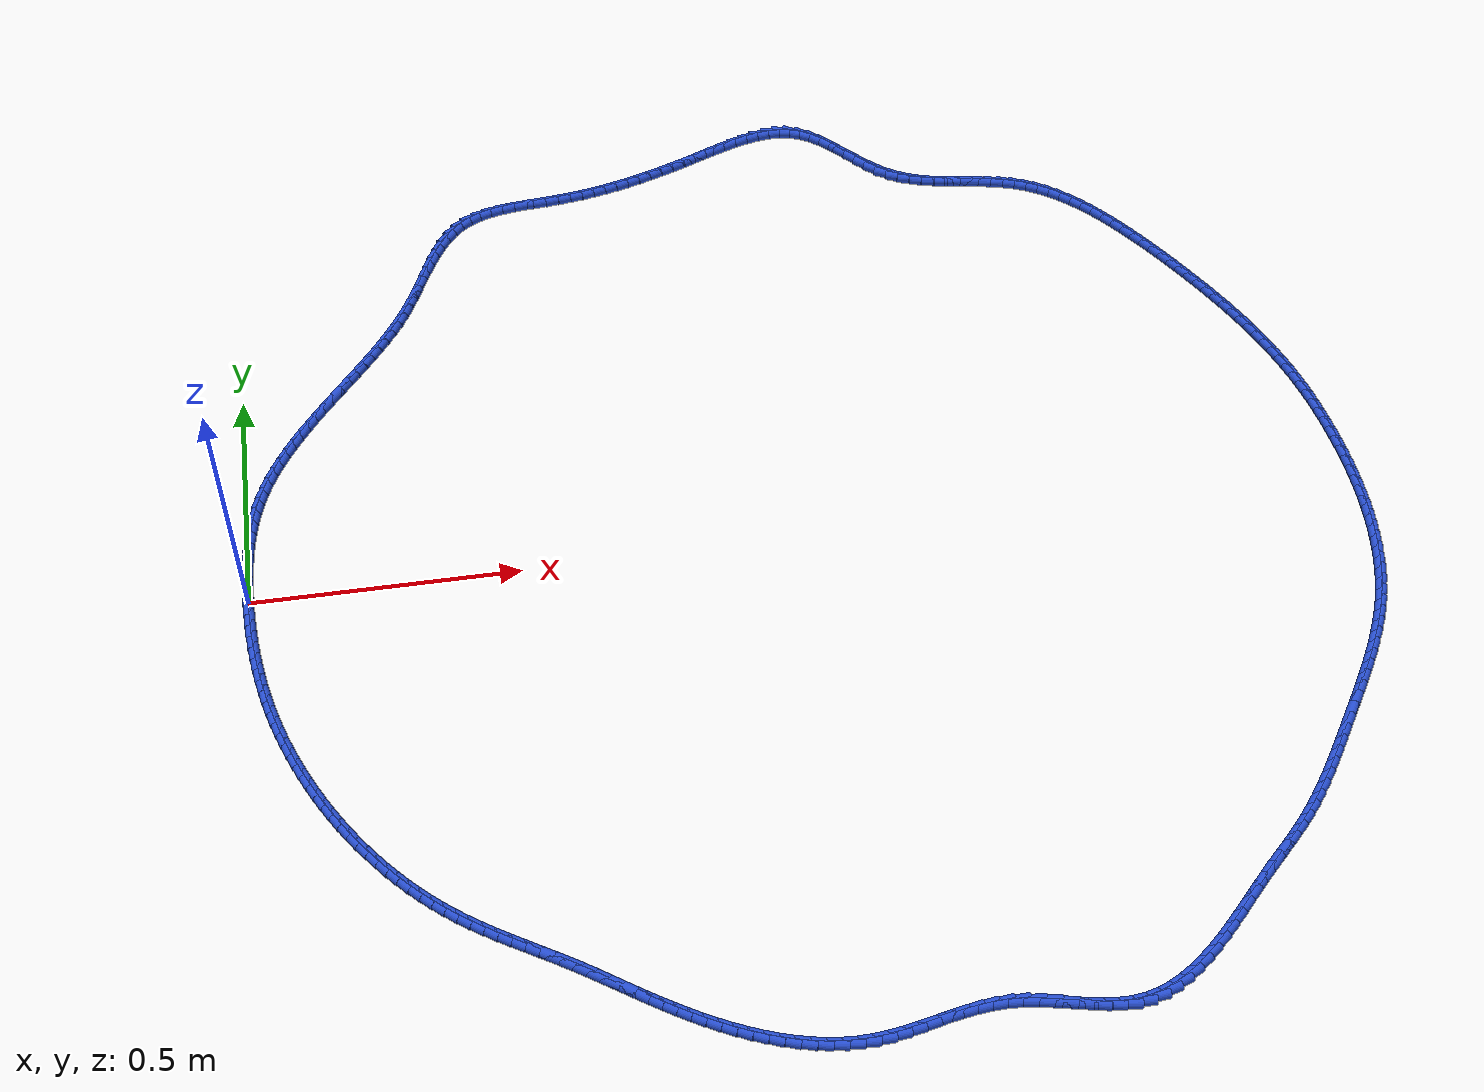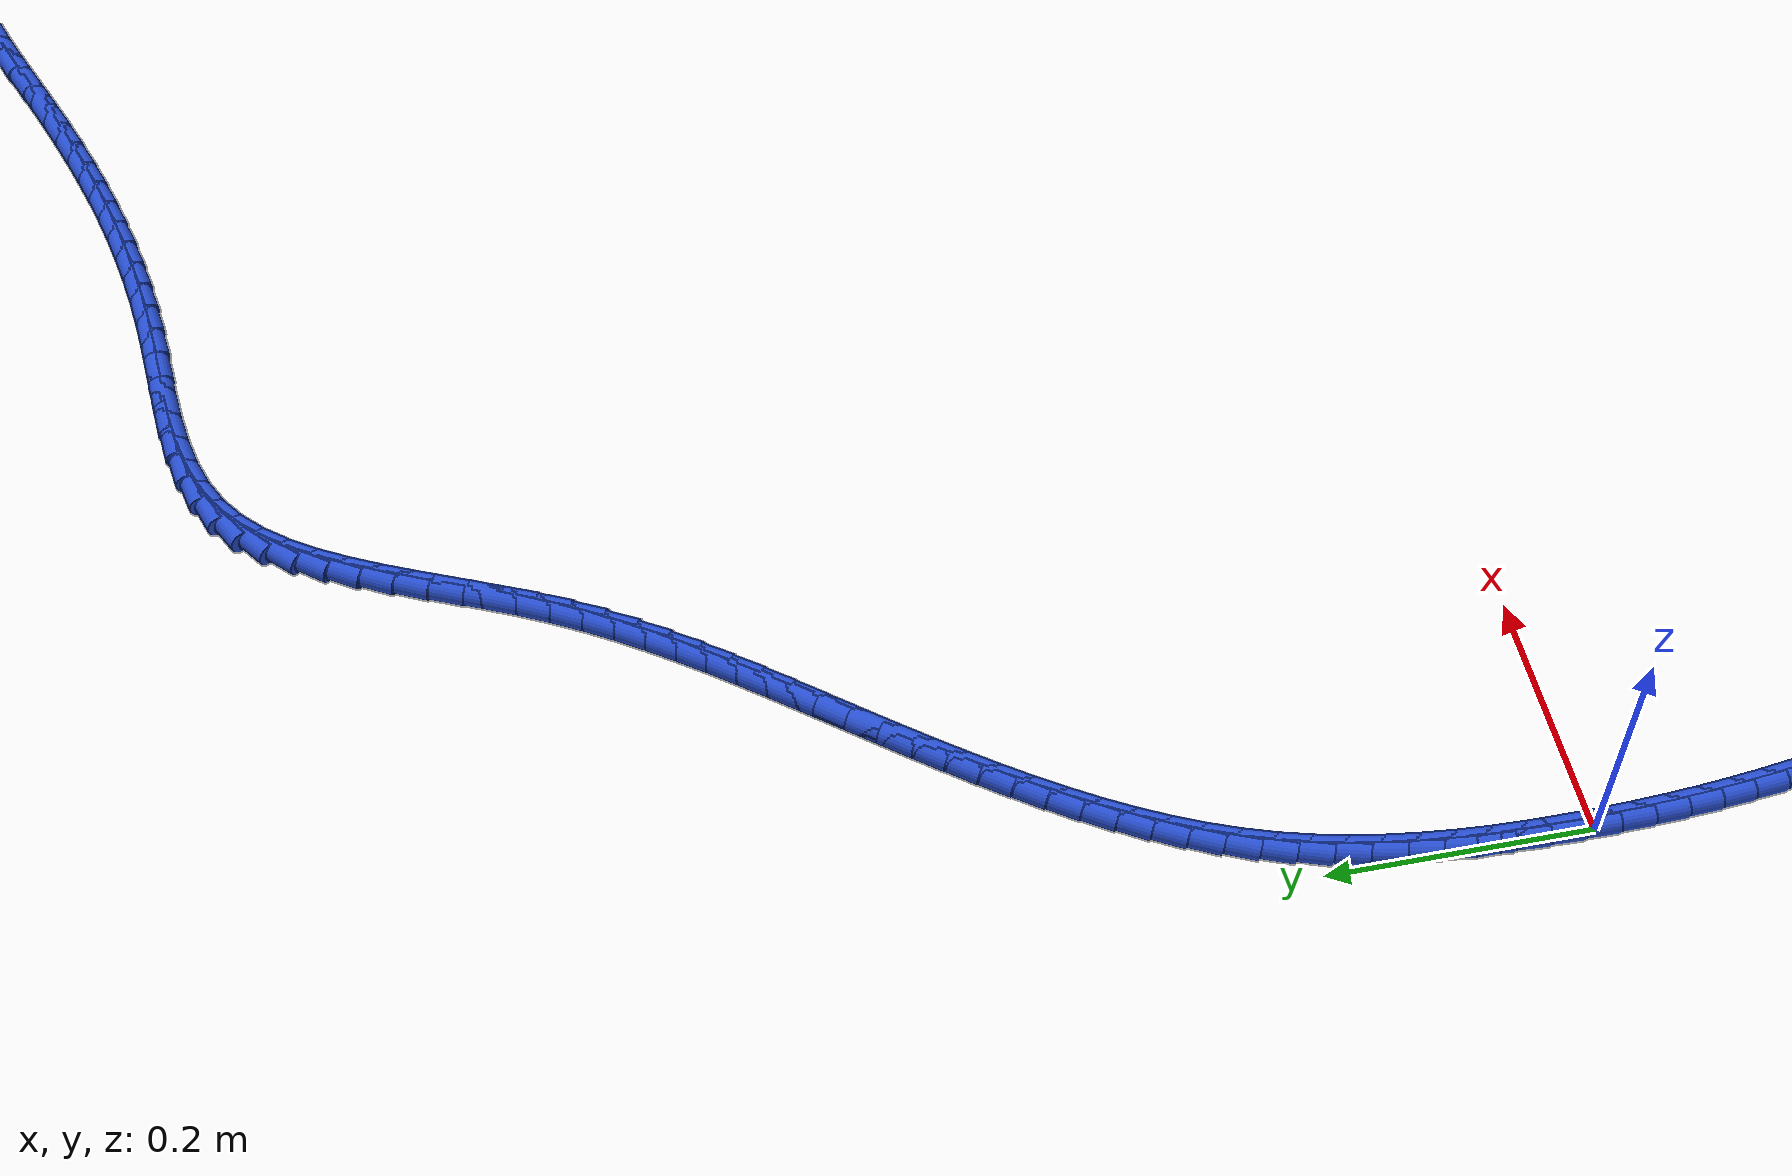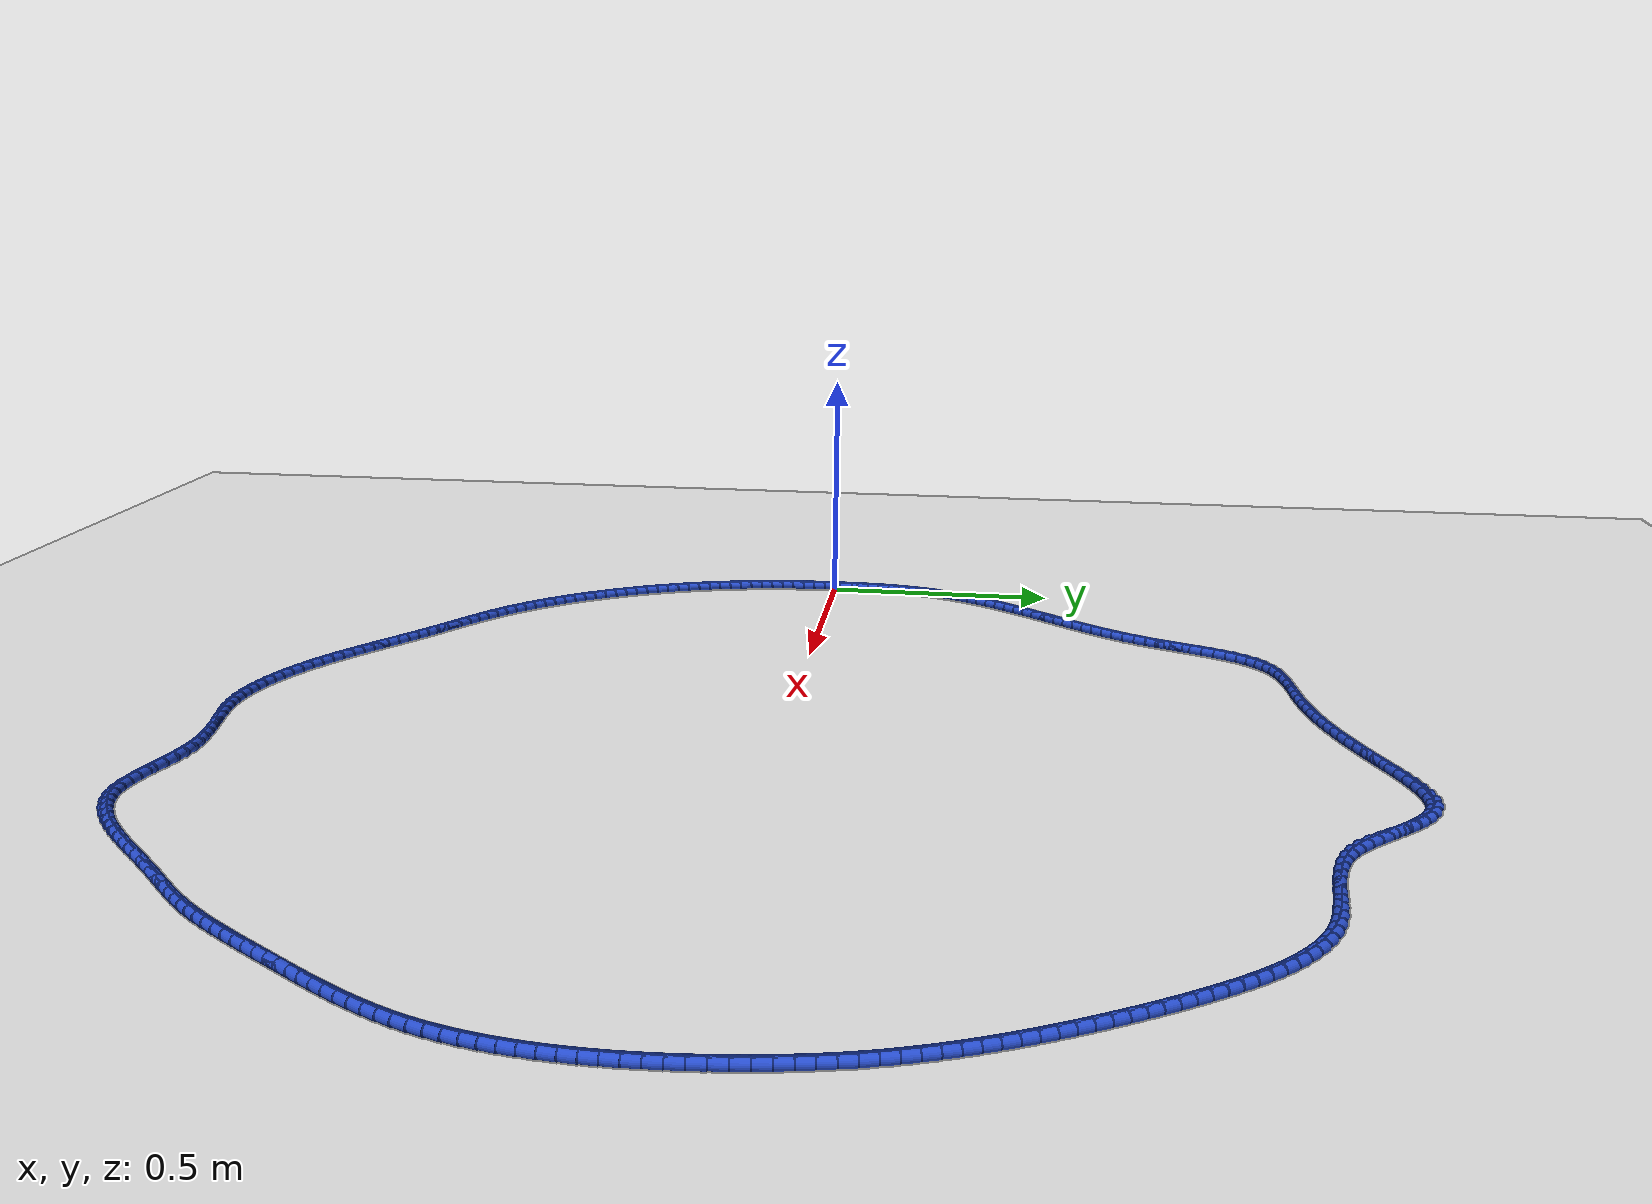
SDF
<sdf version="1.6">
 <world name="default">
  <light name="sun" type="directional">
   <pose>0 0 10 0 -0 0</pose>
   <diffuse>0.8 0.8 0.8 1</diffuse>
   <specular>0.2 0.2 0.2 1</specular>
   <attenuation>
    <range>1000</range>
    <constant>0.9</constant>
    <linear>0.01</linear>
    <quadratic>0.001</quadratic>
   </attenuation>
   <direction>-0.5 0.1 -0.9</direction>
  </light>
  <model name="ground_plane">
   <static>1</static>
   <link name="link">
    <collision name="collision">
     <geometry><plane><normal>0 0 1</normal><size>100 100</size></plane></geometry>
     <surface><friction><ode><mu>100</mu><mu2>50</mu2></ode></friction></surface>
    </collision>
    <visual name="visual">
     <cast_shadows>0</cast_shadows>
     <geometry><plane><normal>0 0 1</normal><size>100 100</size></plane></geometry>
     <material>
      <script><uri>file://media/materials/scripts/gazebo.material</uri><name>Gazebo/WhiteGlow</name></script>
     </material>
    </visual>
   </link>
  </model>
  <gravity>0 0 -9.8</gravity>
  <magnetic_field>6e-06 2.3e-05 -4.2e-05</magnetic_field>
  <atmosphere type="adiabatic"/>
  <physics name="default_physics" default="0" type="ode">
   <max_step_size>0.001</max_step_size>
   <real_time_factor>1</real_time_factor>
   <real_time_update_rate>1000</real_time_update_rate>
  </physics>
  <scene><ambient>0.4 0.4 0.4 1</ambient><background>0.7 0.7 0.7 1</background><shadows>1</shadows></scene>
  <spherical_coordinates>
   <surface_model>EARTH_WGS84</surface_model>
   <latitude_deg>0</latitude_deg>
   <longitude_deg>0</longitude_deg>
   <elevation>0</elevation>
   <heading_deg>0</heading_deg>
  </spherical_coordinates>
  <model name="line">
   <link name="link_0">
    <pose>-1.0842021724855044e-18 2.7755575615628914e-17 0.01 0 1.57 -1.5603251618580196</pose>
    <collision name="collision">
     <geometry><cylinder><radius>0.01</radius><length>0.08</length></cylinder></geometry>
    </collision>
    <visual name="visual">
     <material>
      <script><name>Gazebo/Blue</name><uri>file://media/materials/scripts/gazebo.material</uri></script>
     </material>
     <geometry><cylinder><radius>0.01</radius><length>0.08</length></cylinder></geometry>
    </visual>
   </link>
   <link name="link_1">
    <pose>-0.0002701414424099219 0.02579766155151942 0.01 0 1.57 1.5595440917151902</pose>
    <collision name="collision">
     <geometry><cylinder><radius>0.01</radius><length>0.08</length></cylinder></geometry>
    </collision>
    <visual name="visual">
     <material>
      <script><name>Gazebo/Blue</name><uri>file://media/materials/scripts/gazebo.material</uri></script>
     </material>
     <geometry><cylinder><radius>0.01</radius><length>0.08</length></cylinder></geometry>
    </visual>
   </link>
   <link name="link_2">
    <pose>2.0445288560491106e-05 0.05162137255731039 0.01 0 1.57 1.5342640760914426</pose>
    <collision name="collision">
     <geometry><cylinder><radius>0.01</radius><length>0.08</length></cylinder></geometry>
    </collision>
    <visual name="visual">
     <material>
      <script><name>Gazebo/Blue</name><uri>file://media/materials/scripts/gazebo.material</uri></script>
     </material>
     <geometry><cylinder><radius>0.01</radius><length>0.08</length></cylinder></geometry>
    </visual>
   </link>
   <link name="link_3">
    <pose>0.0009629880714867451 0.07741018709593615 0.01 0 1.57 1.5052798086044072</pose>
    <collision name="collision">
     <geometry><cylinder><radius>0.01</radius><length>0.08</length></cylinder></geometry>
    </collision>
    <visual name="visual">
     <material>
      <script><name>Gazebo/Blue</name><uri>file://media/materials/scripts/gazebo.material</uri></script>
     </material>
     <geometry><cylinder><radius>0.01</radius><length>0.08</length></cylinder></geometry>
    </visual>
   </link>
   <link name="link_4">
    <pose>0.002648714784944347 0.10310315924595989 0.01 0 1.57 1.472425936517467</pose>
    <collision name="collision">
     <geometry><cylinder><radius>0.01</radius><length>0.08</length></cylinder></geometry>
    </collision>
    <visual name="visual">
     <material>
      <script><name>Gazebo/Blue</name><uri>file://media/materials/scripts/gazebo.material</uri></script>
     </material>
     <geometry><cylinder><radius>0.01</radius><length>0.08</length></cylinder></geometry>
    </visual>
   </link>
   <link name="link_5">
    <pose>0.005168853307508804 0.1286393430859448 0.01 0 1.57 1.4355298800457483</pose>
    <collision name="collision">
     <geometry><cylinder><radius>0.01</radius><length>0.08</length></cylinder></geometry>
    </collision>
    <visual name="visual">
     <material>
      <script><name>Gazebo/Blue</name><uri>file://media/materials/scripts/gazebo.material</uri></script>
     </material>
     <geometry><cylinder><radius>0.01</radius><length>0.08</length></cylinder></geometry>
    </visual>
   </link>
   <link name="link_6">
    <pose>0.008614631517755624 0.15395779269445406 0.01 0 1.57 1.3944258125383404</pose>
    <collision name="collision">
     <geometry><cylinder><radius>0.01</radius><length>0.08</length></cylinder></geometry>
    </collision>
    <visual name="visual">
     <material>
      <script><name>Gazebo/Blue</name><uri>file://media/materials/scripts/gazebo.material</uri></script>
     </material>
     <geometry><cylinder><radius>0.01</radius><length>0.08</length></cylinder></geometry>
    </visual>
   </link>
   <link name="link_7">
    <pose>0.013077277294260312 0.17899756215005097 0.01 0 1.57 1.3489729384937394</pose>
    <collision name="collision">
     <geometry><cylinder><radius>0.01</radius><length>0.08</length></cylinder></geometry>
    </collision>
    <visual name="visual">
     <material>
      <script><name>Gazebo/Blue</name><uri>file://media/materials/scripts/gazebo.material</uri></script>
     </material>
     <geometry><cylinder><radius>0.01</radius><length>0.08</length></cylinder></geometry>
    </visual>
   </link>
   <link name="link_8">
    <pose>0.01864801851559838 0.20369770553129862 0.01 0 1.57 1.2990785257821285</pose>
    <collision name="collision">
     <geometry><cylinder><radius>0.01</radius><length>0.08</length></cylinder></geometry>
    </collision>
    <visual name="visual">
     <material>
      <script><name>Gazebo/Blue</name><uri>file://media/materials/scripts/gazebo.material</uri></script>
     </material>
     <geometry><cylinder><radius>0.01</radius><length>0.08</length></cylinder></geometry>
    </visual>
   </link>
   <link name="link_9">
    <pose>0.025418083060345327 0.22799727691676025 0.01 0 1.57 1.2449418229550864</pose>
    <collision name="collision">
     <geometry><cylinder><radius>0.01</radius><length>0.08</length></cylinder></geometry>
    </collision>
    <visual name="visual">
     <material>
      <script><name>Gazebo/Blue</name><uri>file://media/materials/scripts/gazebo.material</uri></script>
     </material>
     <geometry><cylinder><radius>0.01</radius><length>0.08</length></cylinder></geometry>
    </visual>
   </link>
   <link name="link_10">
    <pose>0.033473717230176406 0.25183759924479177 0.01 0 1.57 1.1910577845415524</pose>
    <collision name="collision">
     <geometry><cylinder><radius>0.01</radius><length>0.08</length></cylinder></geometry>
    </collision>
    <visual name="visual">
     <material>
      <script><name>Gazebo/Blue</name><uri>file://media/materials/scripts/gazebo.material</uri></script>
     </material>
     <geometry><cylinder><radius>0.01</radius><length>0.08</length></cylinder></geometry>
    </visual>
   </link>
   <link name="link_11">
    <pose>0.04280025278954684 0.2752059569917476 0.01 0 1.57 1.141720539695457</pose>
    <collision name="collision">
     <geometry><cylinder><radius>0.01</radius><length>0.08</length></cylinder></geometry>
    </collision>
    <visual name="visual">
     <material>
      <script><name>Gazebo/Blue</name><uri>file://media/materials/scripts/gazebo.material</uri></script>
     </material>
     <geometry><cylinder><radius>0.01</radius><length>0.08</length></cylinder></geometry>
    </visual>
   </link>
   <link name="link_12">
    <pose>0.053289159484183765 0.29813238410159343 0.01 0 1.57 1.0972111444542392</pose>
    <collision name="collision">
     <geometry><cylinder><radius>0.01</radius><length>0.08</length></cylinder></geometry>
    </collision>
    <visual name="visual">
     <material>
      <script><name>Gazebo/Blue</name><uri>file://media/materials/scripts/gazebo.material</uri></script>
     </material>
     <geometry><cylinder><radius>0.01</radius><length>0.08</length></cylinder></geometry>
    </visual>
   </link>
   <link name="link_13">
    <pose>0.06482833830782857 0.32064853990681197 0.01 0 1.57 1.0575499763880079</pose>
    <collision name="collision">
     <geometry><cylinder><radius>0.01</radius><length>0.08</length></cylinder></geometry>
    </collision>
    <visual name="visual">
     <material>
      <script><name>Gazebo/Blue</name><uri>file://media/materials/scripts/gazebo.material</uri></script>
     </material>
     <geometry><cylinder><radius>0.01</radius><length>0.08</length></cylinder></geometry>
    </visual>
   </link>
   <link name="link_14">
    <pose>0.0773056902542226 0.3427860837398861 0.01 0 1.57 1.0226829581184442</pose>
    <collision name="collision">
     <geometry><cylinder><radius>0.01</radius><length>0.08</length></cylinder></geometry>
    </collision>
    <visual name="visual">
     <material>
      <script><name>Gazebo/Blue</name><uri>file://media/materials/scripts/gazebo.material</uri></script>
     </material>
     <geometry><cylinder><radius>0.01</radius><length>0.08</length></cylinder></geometry>
    </visual>
   </link>
   <link name="link_15">
    <pose>0.09060911631710718 0.3645766749332985 0.01 0 1.57 0.9925098947791501</pose>
    <collision name="collision">
     <geometry><cylinder><radius>0.01</radius><length>0.08</length></cylinder></geometry>
    </collision>
    <visual name="visual">
     <material>
      <script><name>Gazebo/Blue</name><uri>file://media/materials/scripts/gazebo.material</uri></script>
     </material>
     <geometry><cylinder><radius>0.01</radius><length>0.08</length></cylinder></geometry>
    </visual>
   </link>
   <link name="link_16">
    <pose>0.1046265174902237 0.3860519728195321 0.01 0 1.57 0.9669083268073221</pose>
    <collision name="collision">
     <geometry><cylinder><radius>0.01</radius><length>0.08</length></cylinder></geometry>
    </collision>
    <visual name="visual">
     <material>
      <script><name>Gazebo/Blue</name><uri>file://media/materials/scripts/gazebo.material</uri></script>
     </material>
     <geometry><cylinder><radius>0.01</radius><length>0.08</length></cylinder></geometry>
    </visual>
   </link>
   <link name="link_17">
    <pose>0.1192457947673135 0.40724363673106945 0.01 0 1.57 0.9457525347122957</pose>
    <collision name="collision">
     <geometry><cylinder><radius>0.01</radius><length>0.08</length></cylinder></geometry>
    </collision>
    <visual name="visual">
     <material>
      <script><name>Gazebo/Blue</name><uri>file://media/materials/scripts/gazebo.material</uri></script>
     </material>
     <geometry><cylinder><radius>0.01</radius><length>0.08</length></cylinder></geometry>
    </visual>
   </link>
   <link name="link_18">
    <pose>0.13435484914211787 0.42818332600039344 0.01 0 1.57 0.9289280894465428</pose>
    <collision name="collision">
     <geometry><cylinder><radius>0.01</radius><length>0.08</length></cylinder></geometry>
    </collision>
    <visual name="visual">
     <material>
      <script><name>Gazebo/Blue</name><uri>file://media/materials/scripts/gazebo.material</uri></script>
     </material>
     <geometry><cylinder><radius>0.01</radius><length>0.08</length></cylinder></geometry>
    </visual>
   </link>
   <link name="link_19">
    <pose>0.14984158160837827 0.4489026999599868 0.01 0 1.57 0.9163426927815157</pose>
    <collision name="collision">
     <geometry><cylinder><radius>0.01</radius><length>0.08</length></cylinder></geometry>
    </collision>
    <visual name="visual">
     <material>
      <script><name>Gazebo/Blue</name><uri>file://media/materials/scripts/gazebo.material</uri></script>
     </material>
     <geometry><cylinder><radius>0.01</radius><length>0.08</length></cylinder></geometry>
    </visual>
   </link>
   <link name="link_20">
    <pose>0.16559389315983603 0.46943341794233256 0.01 0 1.57 0.907934130518761</pose>
    <collision name="collision">
     <geometry><cylinder><radius>0.01</radius><length>0.08</length></cylinder></geometry>
    </collision>
    <visual name="visual">
     <material>
      <script><name>Gazebo/Blue</name><uri>file://media/materials/scripts/gazebo.material</uri></script>
     </material>
     <geometry><cylinder><radius>0.01</radius><length>0.08</length></cylinder></geometry>
    </visual>
   </link>
   <link name="link_21">
    <pose>0.18149968479023249 0.48980713927991315 0.01 0 1.57 0.9036760813142651</pose>
    <collision name="collision">
     <geometry><cylinder><radius>0.01</radius><length>0.08</length></cylinder></geometry>
    </collision>
    <visual name="visual">
     <material>
      <script><name>Gazebo/Blue</name><uri>file://media/materials/scripts/gazebo.material</uri></script>
     </material>
     <geometry><cylinder><radius>0.01</radius><length>0.08</length></cylinder></geometry>
    </visual>
   </link>
   <link name="link_22">
    <pose>0.19744685749330892 0.5100555233052114 0.01 0 1.57 0.9035823621691371</pose>
    <collision name="collision">
     <geometry><cylinder><radius>0.01</radius><length>0.08</length></cylinder></geometry>
    </collision>
    <visual name="visual">
     <material>
      <script><name>Gazebo/Blue</name><uri>file://media/materials/scripts/gazebo.material</uri></script>
     </material>
     <geometry><cylinder><radius>0.01</radius><length>0.08</length></cylinder></geometry>
    </visual>
   </link>
   <link name="link_23">
    <pose>0.2133233122628068 0.53021022935071 0.01 0 1.57 0.9077101315692119</pose>
    <collision name="collision">
     <geometry><cylinder><radius>0.01</radius><length>0.08</length></cylinder></geometry>
    </collision>
    <visual name="visual">
     <material>
      <script><name>Gazebo/Blue</name><uri>file://media/materials/scripts/gazebo.material</uri></script>
     </material>
     <geometry><cylinder><radius>0.01</radius><length>0.08</length></cylinder></geometry>
    </visual>
   </link>
   <link name="link_24">
    <pose>0.22901695977784772 0.550302935023541 0.01 0 1.57 0.9163340492836096</pose>
    <collision name="collision">
     <geometry><cylinder><radius>0.01</radius><length>0.08</length></cylinder></geometry>
    </collision>
    <visual name="visual">
     <material>
      <script><name>Gazebo/Blue</name><uri>file://media/materials/scripts/gazebo.material</uri></script>
     </material>
     <geometry><cylinder><radius>0.01</radius><length>0.08</length></cylinder></geometry>
    </visual>
   </link>
   <link name="link_25">
    <pose>0.24442798814996167 0.5703884833366913 0.01 0 1.57 0.9300379514819116</pose>
    <collision name="collision">
     <geometry><cylinder><radius>0.01</radius><length>0.08</length></cylinder></geometry>
    </collision>
    <visual name="visual">
     <material>
      <script><name>Gazebo/Blue</name><uri>file://media/materials/scripts/gazebo.material</uri></script>
     </material>
     <geometry><cylinder><radius>0.01</radius><length>0.08</length></cylinder></geometry>
    </visual>
   </link>
   <link name="link_26">
    <pose>0.2594928864295115 0.5905902109387106 0.01 0 1.57 0.9488639191968582</pose>
    <collision name="collision">
     <geometry><cylinder><radius>0.01</radius><length>0.08</length></cylinder></geometry>
    </collision>
    <visual name="visual">
     <material>
      <script><name>Gazebo/Blue</name><uri>file://media/materials/scripts/gazebo.material</uri></script>
     </material>
     <geometry><cylinder><radius>0.01</radius><length>0.08</length></cylinder></geometry>
    </visual>
   </link>
   <link name="link_27">
    <pose>0.2741548206432137 0.611044052785512 0.01 0 1.57 0.9726475083411117</pose>
    <collision name="collision">
     <geometry><cylinder><radius>0.01</radius><length>0.08</length></cylinder></geometry>
    </collision>
    <visual name="visual">
     <material>
      <script><name>Gazebo/Blue</name><uri>file://media/materials/scripts/gazebo.material</uri></script>
     </material>
     <geometry><cylinder><radius>0.01</radius><length>0.08</length></cylinder></geometry>
    </visual>
   </link>
   <link name="link_28">
    <pose>0.2883569568177839 0.6318859438330072 0.01 0 1.57 1.0011065653233218</pose>
    <collision name="collision">
     <geometry><cylinder><radius>0.01</radius><length>0.08</length></cylinder></geometry>
    </collision>
    <visual name="visual">
     <material>
      <script><name>Gazebo/Blue</name><uri>file://media/materials/scripts/gazebo.material</uri></script>
     </material>
     <geometry><cylinder><radius>0.01</radius><length>0.08</length></cylinder></geometry>
    </visual>
   </link>
   <link name="link_29">
    <pose>0.3020424609799387 0.6532518190371102 0.01 0 1.57 1.0338370995341764</pose>
    <collision name="collision">
     <geometry><cylinder><radius>0.01</radius><length>0.08</length></cylinder></geometry>
    </collision>
    <visual name="visual">
     <material>
      <script><name>Gazebo/Blue</name><uri>file://media/materials/scripts/gazebo.material</uri></script>
     </material>
     <geometry><cylinder><radius>0.01</radius><length>0.08</length></cylinder></geometry>
    </visual>
   </link>
   <link name="link_30">
    <pose>0.315154499156394 0.6752776133537328 0.01 0 1.57 1.070316749736388</pose>
    <collision name="collision">
     <geometry><cylinder><radius>0.01</radius><length>0.08</length></cylinder></geometry>
    </collision>
    <visual name="visual">
     <material>
      <script><name>Gazebo/Blue</name><uri>file://media/materials/scripts/gazebo.material</uri></script>
     </material>
     <geometry><cylinder><radius>0.01</radius><length>0.08</length></cylinder></geometry>
    </visual>
   </link>
   <link name="link_31">
    <pose>0.3276362373738661 0.6980992617387883 0.01 0 1.57 1.1097260973705472</pose>
    <collision name="collision">
     <geometry><cylinder><radius>0.01</radius><length>0.08</length></cylinder></geometry>
    </collision>
    <visual name="visual">
     <material>
      <script><name>Gazebo/Blue</name><uri>file://media/materials/scripts/gazebo.material</uri></script>
     </material>
     <geometry><cylinder><radius>0.01</radius><length>0.08</length></cylinder></geometry>
    </visual>
   </link>
   <link name="link_32">
    <pose>0.3394340397560818 0.7218476916932017 0.01 0 1.57 1.1433270966369884</pose>
    <collision name="collision">
     <geometry><cylinder><radius>0.01</radius><length>0.08</length></cylinder></geometry>
    </collision>
    <visual name="visual">
     <material>
      <script><name>Gazebo/Blue</name><uri>file://media/materials/scripts/gazebo.material</uri></script>
     </material>
     <geometry><cylinder><radius>0.01</radius><length>0.08</length></cylinder></geometry>
    </visual>
   </link>
   <link name="link_33">
    <pose>0.35063463756392504 0.7464340493545889 0.01 0 1.57 1.160743811272451</pose>
    <collision name="collision">
     <geometry><cylinder><radius>0.01</radius><length>0.08</length></cylinder></geometry>
    </collision>
    <visual name="visual">
     <material>
      <script><name>Gazebo/Blue</name><uri>file://media/materials/scripts/gazebo.material</uri></script>
     </material>
     <geometry><cylinder><radius>0.01</radius><length>0.08</length></cylinder></geometry>
    </visual>
   </link>
   <link name="link_34">
    <pose>0.3615169680846194 0.7714685321957914 0.01 0 1.57 1.162131566819311</pose>
    <collision name="collision">
     <geometry><cylinder><radius>0.01</radius><length>0.08</length></cylinder></geometry>
    </collision>
    <visual name="visual">
     <material>
      <script><name>Gazebo/Blue</name><uri>file://media/materials/scripts/gazebo.material</uri></script>
     </material>
     <geometry><cylinder><radius>0.01</radius><length>0.08</length></cylinder></geometry>
    </visual>
   </link>
   <link name="link_35">
    <pose>0.3723738566156871 0.7965395923873043 0.01 0 1.57 1.1475709959268725</pose>
    <collision name="collision">
     <geometry><cylinder><radius>0.01</radius><length>0.08</length></cylinder></geometry>
    </collision>
    <visual name="visual">
     <material>
      <script><name>Gazebo/Blue</name><uri>file://media/materials/scripts/gazebo.material</uri></script>
     </material>
     <geometry><cylinder><radius>0.01</radius><length>0.08</length></cylinder></geometry>
    </visual>
   </link>
   <link name="link_36">
    <pose>0.38349812845465053 0.8212356820996223 0.01 0 1.57 1.1162338055828172</pose>
    <collision name="collision">
     <geometry><cylinder><radius>0.01</radius><length>0.08</length></cylinder></geometry>
    </collision>
    <visual name="visual">
     <material>
      <script><name>Gazebo/Blue</name><uri>file://media/materials/scripts/gazebo.material</uri></script>
     </material>
     <geometry><cylinder><radius>0.01</radius><length>0.08</length></cylinder></geometry>
    </visual>
   </link>
   <link name="link_37">
    <pose>0.3951826088990318 0.8451452535032395 0.01 0 1.57 1.066393140241032</pose>
    <collision name="collision">
     <geometry><cylinder><radius>0.01</radius><length>0.08</length></cylinder></geometry>
    </collision>
    <visual name="visual">
     <material>
      <script><name>Gazebo/Blue</name><uri>file://media/materials/scripts/gazebo.material</uri></script>
     </material>
     <geometry><cylinder><radius>0.01</radius><length>0.08</length></cylinder></geometry>
    </visual>
   </link>
   <link name="link_38">
    <pose>0.40772012324635337 0.8678567587686514 0.01 0 1.57 0.9955164419304721</pose>
    <collision name="collision">
     <geometry><cylinder><radius>0.01</radius><length>0.08</length></cylinder></geometry>
    </collision>
    <visual name="visual">
     <material>
      <script><name>Gazebo/Blue</name><uri>file://media/materials/scripts/gazebo.material</uri></script>
     </material>
     <geometry><cylinder><radius>0.01</radius><length>0.08</length></cylinder></geometry>
    </visual>
   </link>
   <link name="link_39">
    <pose>0.4214034967941377 0.8889586500663526 0.01 0 1.57 0.9006266477489238</pose>
    <collision name="collision">
     <geometry><cylinder><radius>0.01</radius><length>0.08</length></cylinder></geometry>
    </collision>
    <visual name="visual">
     <material>
      <script><name>Gazebo/Blue</name><uri>file://media/materials/scripts/gazebo.material</uri></script>
     </material>
     <geometry><cylinder><radius>0.01</radius><length>0.08</length></cylinder></geometry>
    </visual>
   </link>
   <link name="link_40">
    <pose>0.4365255548399066 0.908039379566837 0.01 0 1.57 0.779262770946666</pose>
    <collision name="collision">
     <geometry><cylinder><radius>0.01</radius><length>0.08</length></cylinder></geometry>
    </collision>
    <visual name="visual">
     <material>
      <script><name>Gazebo/Blue</name><uri>file://media/materials/scripts/gazebo.material</uri></script>
     </material>
     <geometry><cylinder><radius>0.01</radius><length>0.08</length></cylinder></geometry>
    </visual>
   </link>
   <link name="link_41">
    <pose>0.45337912268118297 0.9246873994406006 0.01 0 1.57 0.6313684167849426</pose>
    <collision name="collision">
     <geometry><cylinder><radius>0.01</radius><length>0.08</length></cylinder></geometry>
    </collision>
    <visual name="visual">
     <material>
      <script><name>Gazebo/Blue</name><uri>file://media/materials/scripts/gazebo.material</uri></script>
     </material>
     <geometry><cylinder><radius>0.01</radius><length>0.08</length></cylinder></geometry>
    </visual>
   </link>
   <link name="link_42">
    <pose>0.47225702561548877 0.9384911618581371 0.01 0 1.57 0.46972101029280466</pose>
    <collision name="collision">
     <geometry><cylinder><radius>0.01</radius><length>0.08</length></cylinder></geometry>
    </collision>
    <visual name="visual">
     <material>
      <script><name>Gazebo/Blue</name><uri>file://media/materials/scripts/gazebo.material</uri></script>
     </material>
     <geometry><cylinder><radius>0.01</radius><length>0.08</length></cylinder></geometry>
    </visual>
   </link>
   <link name="link_43">
    <pose>0.4933393461675404 0.9491928633648444 0.01 0 1.57 0.3335622631278988</pose>
    <collision name="collision">
     <geometry><cylinder><radius>0.01</radius><length>0.08</length></cylinder></geometry>
    </collision>
    <visual name="visual">
     <material>
      <script><name>Gazebo/Blue</name><uri>file://media/materials/scripts/gazebo.material</uri></script>
     </material>
     <geometry><cylinder><radius>0.01</radius><length>0.08</length></cylinder></geometry>
    </visual>
   </link>
   <link name="link_44">
    <pose>0.5163444330852082 0.957164354799033 0.01 0 1.57 0.23120673856762497</pose>
    <collision name="collision">
     <geometry><cylinder><radius>0.01</radius><length>0.08</length></cylinder></geometry>
    </collision>
    <visual name="visual">
     <material>
      <script><name>Gazebo/Blue</name><uri>file://media/materials/scripts/gazebo.material</uri></script>
     </material>
     <geometry><cylinder><radius>0.01</radius><length>0.08</length></cylinder></geometry>
    </visual>
   </link>
   <link name="link_45">
    <pose>0.5408724470964811 0.9629386569151468 0.01 0 1.57 0.15888170208426286</pose>
    <collision name="collision">
     <geometry><cylinder><radius>0.01</radius><length>0.08</length></cylinder></geometry>
    </collision>
    <visual name="visual">
     <material>
      <script><name>Gazebo/Blue</name><uri>file://media/materials/scripts/gazebo.material</uri></script>
     </material>
     <geometry><cylinder><radius>0.01</radius><length>0.08</length></cylinder></geometry>
    </visual>
   </link>
   <link name="link_46">
    <pose>0.5665235488732592 0.9670487905441177 0.01 0 1.57 0.11247343270974473</pose>
    <collision name="collision">
     <geometry><cylinder><radius>0.01</radius><length>0.08</length></cylinder></geometry>
    </collision>
    <visual name="visual">
     <material>
      <script><name>Gazebo/Blue</name><uri>file://media/materials/scripts/gazebo.material</uri></script>
     </material>
     <geometry><cylinder><radius>0.01</radius><length>0.08</length></cylinder></geometry>
    </visual>
   </link>
   <link name="link_47">
    <pose>0.5928978990874411 0.9700277765168769 0.01 0 1.57 0.08894295581526128</pose>
    <collision name="collision">
     <geometry><cylinder><radius>0.01</radius><length>0.08</length></cylinder></geometry>
    </collision>
    <visual name="visual">
     <material>
      <script><name>Gazebo/Blue</name><uri>file://media/materials/scripts/gazebo.material</uri></script>
     </material>
     <geometry><cylinder><radius>0.01</radius><length>0.08</length></cylinder></geometry>
    </visual>
   </link>
   <link name="link_48">
    <pose>0.6195956584109259 0.9724086356643556 0.01 0 1.57 0.08677021354866554</pose>
    <collision name="collision">
     <geometry><cylinder><radius>0.01</radius><length>0.08</length></cylinder></geometry>
    </collision>
    <visual name="visual">
     <material>
      <script><name>Gazebo/Blue</name><uri>file://media/materials/scripts/gazebo.material</uri></script>
     </material>
     <geometry><cylinder><radius>0.01</radius><length>0.08</length></cylinder></geometry>
    </visual>
   </link>
   <link name="link_49">
    <pose>0.6462169875156133 0.974724388817486 0.01 0 1.57 0.10562375270156373</pose>
    <collision name="collision">
     <geometry><cylinder><radius>0.01</radius><length>0.08</length></cylinder></geometry>
    </collision>
    <visual name="visual">
     <material>
      <script><name>Gazebo/Blue</name><uri>file://media/materials/scripts/gazebo.material</uri></script>
     </material>
     <geometry><cylinder><radius>0.01</radius><length>0.08</length></cylinder></geometry>
    </visual>
   </link>
   <link name="link_50">
    <pose>0.6723718752097325 0.977497285712734 0.01 0 1.57 0.13590932357505975</pose>
    <collision name="collision">
     <geometry><cylinder><radius>0.01</radius><length>0.08</length></cylinder></geometry>
    </collision>
    <visual name="visual">
     <material>
      <script><name>Gazebo/Blue</name><uri>file://media/materials/scripts/gazebo.material</uri></script>
     </material>
     <geometry><cylinder><radius>0.01</radius><length>0.08</length></cylinder></geometry>
    </visual>
   </link>
   <link name="link_51">
    <pose>0.6979077324628169 0.9809893745140837 0.01 0 1.57 0.16662600839541872</pose>
    <collision name="collision">
     <geometry><cylinder><radius>0.01</radius><length>0.08</length></cylinder></geometry>
    </collision>
    <visual name="visual">
     <material>
      <script><name>Gazebo/Blue</name><uri>file://media/materials/scripts/gazebo.material</uri></script>
     </material>
     <geometry><cylinder><radius>0.01</radius><length>0.08</length></cylinder></geometry>
    </visual>
   </link>
   <link name="link_52">
    <pose>0.7229158892675106 0.9851953816114157 0.01 0 1.57 0.19684295325530418</pose>
    <collision name="collision">
     <geometry><cylinder><radius>0.01</radius><length>0.08</length></cylinder></geometry>
    </collision>
    <visual name="visual">
     <material>
      <script><name>Gazebo/Blue</name><uri>file://media/materials/scripts/gazebo.material</uri></script>
     </material>
     <geometry><cylinder><radius>0.01</radius><length>0.08</length></cylinder></geometry>
    </visual>
   </link>
   <link name="link_53">
    <pose>0.7474988034220208 0.9900978379344654 0.01 0 1.57 0.22613128917392974</pose>
    <collision name="collision">
     <geometry><cylinder><radius>0.01</radius><length>0.08</length></cylinder></geometry>
    </collision>
    <visual name="visual">
     <material>
      <script><name>Gazebo/Blue</name><uri>file://media/materials/scripts/gazebo.material</uri></script>
     </material>
     <geometry><cylinder><radius>0.01</radius><length>0.08</length></cylinder></geometry>
    </visual>
   </link>
   <link name="link_54">
    <pose>0.7717589327245552 0.995679274412968 0.01 0 1.57 0.25407966554252204</pose>
    <collision name="collision">
     <geometry><cylinder><radius>0.01</radius><length>0.08</length></cylinder></geometry>
    </collision>
    <visual name="visual">
     <material>
      <script><name>Gazebo/Blue</name><uri>file://media/materials/scripts/gazebo.material</uri></script>
     </material>
     <geometry><cylinder><radius>0.01</radius><length>0.08</length></cylinder></geometry>
    </visual>
   </link>
   <link name="link_55">
    <pose>0.7957987349733203 1.0019222219766581 0.01 0 1.57 0.28031403623677137</pose>
    <collision name="collision">
     <geometry><cylinder><radius>0.01</radius><length>0.08</length></cylinder></geometry>
    </collision>
    <visual name="visual">
     <material>
      <script><name>Gazebo/Blue</name><uri>file://media/materials/scripts/gazebo.material</uri></script>
     </material>
     <geometry><cylinder><radius>0.01</radius><length>0.08</length></cylinder></geometry>
    </visual>
   </link>
   <link name="link_56">
    <pose>0.819720667966524 1.0088092115552716 0.01 0 1.57 0.3045140934398461</pose>
    <collision name="collision">
     <geometry><cylinder><radius>0.01</radius><length>0.08</length></cylinder></geometry>
    </collision>
    <visual name="visual">
     <material>
      <script><name>Gazebo/Blue</name><uri>file://media/materials/scripts/gazebo.material</uri></script>
     </material>
     <geometry><cylinder><radius>0.01</radius><length>0.08</length></cylinder></geometry>
    </visual>
   </link>
   <link name="link_57">
    <pose>0.8436271895023728 1.0163227740785428 0.01 0 1.57 0.32642487195838027</pose>
    <collision name="collision">
     <geometry><cylinder><radius>0.01</radius><length>0.08</length></cylinder></geometry>
    </collision>
    <visual name="visual">
     <material>
      <script><name>Gazebo/Blue</name><uri>file://media/materials/scripts/gazebo.material</uri></script>
     </material>
     <geometry><cylinder><radius>0.01</radius><length>0.08</length></cylinder></geometry>
    </visual>
   </link>
   <link name="link_58">
    <pose>0.8676207573790748 1.0244454404762078 0.01 0 1.57 0.34586287224030565</pose>
    <collision name="collision">
     <geometry><cylinder><radius>0.01</radius><length>0.08</length></cylinder></geometry>
    </collision>
    <visual name="visual">
     <material>
      <script><name>Gazebo/Blue</name><uri>file://media/materials/scripts/gazebo.material</uri></script>
     </material>
     <geometry><cylinder><radius>0.01</radius><length>0.08</length></cylinder></geometry>
    </visual>
   </link>
   <link name="link_59">
    <pose>0.8918038293948365 1.033159741678001 0.01 0 1.57 0.3627168683392079</pose>
    <collision name="collision">
     <geometry><cylinder><radius>0.01</radius><length>0.08</length></cylinder></geometry>
    </collision>
    <visual name="visual">
     <material>
      <script><name>Gazebo/Blue</name><uri>file://media/materials/scripts/gazebo.material</uri></script>
     </material>
     <geometry><cylinder><radius>0.01</radius><length>0.08</length></cylinder></geometry>
    </visual>
   </link>
   <link name="link_60">
    <pose>0.9162788633478655 1.0424482086136582 0.01 0 1.57 0.3769442014996162</pose>
    <collision name="collision">
     <geometry><cylinder><radius>0.01</radius><length>0.08</length></cylinder></geometry>
    </collision>
    <visual name="visual">
     <material>
      <script><name>Gazebo/Blue</name><uri>file://media/materials/scripts/gazebo.material</uri></script>
     </material>
     <geometry><cylinder><radius>0.01</radius><length>0.08</length></cylinder></geometry>
    </visual>
   </link>
   <link name="link_61">
    <pose>0.9411483170363688 1.0522933722129142 0.01 0 1.57 0.38824361382712885</pose>
    <collision name="collision">
     <geometry><cylinder><radius>0.01</radius><length>0.08</length></cylinder></geometry>
    </collision>
    <visual name="visual">
     <material>
      <script><name>Gazebo/Blue</name><uri>file://media/materials/scripts/gazebo.material</uri></script>
     </material>
     <geometry><cylinder><radius>0.01</radius><length>0.08</length></cylinder></geometry>
    </visual>
   </link>
   <link name="link_62">
    <pose>0.9665073764416161 1.0626653096304959 0.01 0 1.57 0.389977952783943</pose>
    <collision name="collision">
     <geometry><cylinder><radius>0.01</radius><length>0.08</length></cylinder></geometry>
    </collision>
    <visual name="visual">
     <material>
      <script><name>Gazebo/Blue</name><uri>file://media/materials/scripts/gazebo.material</uri></script>
     </material>
     <geometry><cylinder><radius>0.01</radius><length>0.08</length></cylinder></geometry>
    </visual>
   </link>
   <link name="link_63">
    <pose>0.9922936424413037 1.073264216443884 0.01 0 1.57 0.3760422464208623</pose>
    <collision name="collision">
     <geometry><cylinder><radius>0.01</radius><length>0.08</length></cylinder></geometry>
    </collision>
    <visual name="visual">
     <material>
      <script><name>Gazebo/Blue</name><uri>file://media/materials/scripts/gazebo.material</uri></script>
     </material>
     <geometry><cylinder><radius>0.01</radius><length>0.08</length></cylinder></geometry>
    </visual>
   </link>
   <link name="link_64">
    <pose>1.0182923211491122 1.0835292956726101 0.01 0 1.57 0.3456698950445351</pose>
    <collision name="collision">
     <geometry><cylinder><radius>0.01</radius><length>0.08</length></cylinder></geometry>
    </collision>
    <visual name="visual">
     <material>
      <script><name>Gazebo/Blue</name><uri>file://media/materials/scripts/gazebo.material</uri></script>
     </material>
     <geometry><cylinder><radius>0.01</radius><length>0.08</length></cylinder></geometry>
    </visual>
   </link>
   <link name="link_65">
    <pose>1.0442823852947185 1.0928890749901967 0.01 0 1.57 0.29696353346140586</pose>
    <collision name="collision">
     <geometry><cylinder><radius>0.01</radius><length>0.08</length></cylinder></geometry>
    </collision>
    <visual name="visual">
     <material>
      <script><name>Gazebo/Blue</name><uri>file://media/materials/scripts/gazebo.material</uri></script>
     </material>
     <geometry><cylinder><radius>0.01</radius><length>0.08</length></cylinder></geometry>
    </visual>
   </link>
   <link name="link_66">
    <pose>1.0700428076078006 1.1007720820701667 0.01 0 1.57 0.22657564463094484</pose>
    <collision name="collision">
     <geometry><cylinder><radius>0.01</radius><length>0.08</length></cylinder></geometry>
    </collision>
    <visual name="visual">
     <material>
      <script><name>Gazebo/Blue</name><uri>file://media/materials/scripts/gazebo.material</uri></script>
     </material>
     <geometry><cylinder><radius>0.01</radius><length>0.08</length></cylinder></geometry>
    </visual>
   </link>
   <link name="link_67">
    <pose>1.0953525608180354 1.1066068445860413 0.01 0 1.57 0.12975785164470752</pose>
    <collision name="collision">
     <geometry><cylinder><radius>0.01</radius><length>0.08</length></cylinder></geometry>
    </collision>
    <visual name="visual">
     <material>
      <script><name>Gazebo/Blue</name><uri>file://media/materials/scripts/gazebo.material</uri></script>
     </material>
     <geometry><cylinder><radius>0.01</radius><length>0.08</length></cylinder></geometry>
    </visual>
   </link>
   <link name="link_68">
    <pose>1.1199906176551 1.1098218902113446 0.01 0 1.57 0.001004677425764139</pose>
    <collision name="collision">
     <geometry><cylinder><radius>0.01</radius><length>0.08</length></cylinder></geometry>
    </collision>
    <visual name="visual">
     <material>
      <script><name>Gazebo/Blue</name><uri>file://media/materials/scripts/gazebo.material</uri></script>
     </material>
     <geometry><cylinder><radius>0.01</radius><length>0.08</length></cylinder></geometry>
    </visual>
   </link>
   <link name="link_69">
    <pose>1.1437359508486715 1.1098457466195981 0.01 0 1.57 -0.16372422563406325</pose>
    <collision name="collision">
     <geometry><cylinder><radius>0.01</radius><length>0.08</length></cylinder></geometry>
    </collision>
    <visual name="visual">
     <material>
      <script><name>Gazebo/Blue</name><uri>file://media/materials/scripts/gazebo.material</uri></script>
     </material>
     <geometry><cylinder><radius>0.01</radius><length>0.08</length></cylinder></geometry>
    </visual>
   </link>
   <link name="link_70">
    <pose>1.1663675331284278 1.1061069414843239 0.01 0 1.57 -0.35898097212196867</pose>
    <collision name="collision">
     <geometry><cylinder><radius>0.01</radius><length>0.08</length></cylinder></geometry>
    </collision>
    <visual name="visual">
     <material>
      <script><name>Gazebo/Blue</name><uri>file://media/materials/scripts/gazebo.material</uri></script>
     </material>
     <geometry><cylinder><radius>0.01</radius><length>0.08</length></cylinder></geometry>
    </visual>
   </link>
   <link name="link_71">
    <pose>1.1876910863482864 1.098105493624344 0.01 0 1.57 -0.5365407657694464</pose>
    <collision name="collision">
     <geometry><cylinder><radius>0.01</radius><length>0.08</length></cylinder></geometry>
    </collision>
    <visual name="visual">
     <material>
      <script><name>Gazebo/Blue</name><uri>file://media/materials/scripts/gazebo.material</uri></script>
     </material>
     <geometry><cylinder><radius>0.01</radius><length>0.08</length></cylinder></geometry>
    </visual>
   </link>
   <link name="link_72">
    <pose>1.2078109316426904 1.086139474323957 0.01 0 1.57 -0.667300120723335</pose>
    <collision name="collision">
     <geometry><cylinder><radius>0.01</radius><length>0.08</length></cylinder></geometry>
    </collision>
    <visual name="visual">
     <material>
      <script><name>Gazebo/Blue</name><uri>file://media/materials/scripts/gazebo.material</uri></script>
     </material>
     <geometry><cylinder><radius>0.01</radius><length>0.08</length></cylinder></geometry>
    </visual>
   </link>
   <link name="link_73">
    <pose>1.2270183240638377 1.0710065644903806 0.01 0 1.57 -0.7550719745141673</pose>
    <collision name="collision">
     <geometry><cylinder><radius>0.01</radius><length>0.08</length></cylinder></geometry>
    </collision>
    <visual name="visual">
     <material>
      <script><name>Gazebo/Blue</name><uri>file://media/materials/scripts/gazebo.material</uri></script>
     </material>
     <geometry><cylinder><radius>0.01</radius><length>0.08</length></cylinder></geometry>
    </visual>
   </link>
   <link name="link_74">
    <pose>1.2456073874216205 1.0535121122266344 0.01 0 1.57 -0.8064530137730368</pose>
    <collision name="collision">
     <geometry><cylinder><radius>0.01</radius><length>0.08</length></cylinder></geometry>
    </collision>
    <visual name="visual">
     <material>
      <script><name>Gazebo/Blue</name><uri>file://media/materials/scripts/gazebo.material</uri></script>
     </material>
     <geometry><cylinder><radius>0.01</radius><length>0.08</length></cylinder></geometry>
    </visual>
   </link>
   <link name="link_75">
    <pose>1.2638722455259312 1.034461465635738 0.01 0 1.57 -0.8265649506673421</pose>
    <collision name="collision">
     <geometry><cylinder><radius>0.01</radius><length>0.08</length></cylinder></geometry>
    </collision>
    <visual name="visual">
     <material>
      <script><name>Gazebo/Blue</name><uri>file://media/materials/scripts/gazebo.material</uri></script>
     </material>
     <geometry><cylinder><radius>0.01</radius><length>0.08</length></cylinder></geometry>
    </visual>
   </link>
   <link name="link_76">
    <pose>1.2821070221866606 1.0146599728207117 0.01 0 1.57 -0.8180221046899048</pose>
    <collision name="collision">
     <geometry><cylinder><radius>0.01</radius><length>0.08</length></cylinder></geometry>
    </collision>
    <visual name="visual">
     <material>
      <script><name>Gazebo/Blue</name><uri>file://media/materials/scripts/gazebo.material</uri></script>
     </material>
     <geometry><cylinder><radius>0.01</radius><length>0.08</length></cylinder></geometry>
    </visual>
   </link>
   <link name="link_77">
    <pose>1.3006058412137014 0.9949129818845748 0.01 0 1.57 -0.780922026195444</pose>
    <collision name="collision">
     <geometry><cylinder><radius>0.01</radius><length>0.08</length></cylinder></geometry>
    </collision>
    <visual name="visual">
     <material>
      <script><name>Gazebo/Blue</name><uri>file://media/materials/scripts/gazebo.material</uri></script>
     </material>
     <geometry><cylinder><radius>0.01</radius><length>0.08</length></cylinder></geometry>
    </visual>
   </link>
   <link name="link_78">
    <pose>1.3196628264169445 0.9760258409303462 0.01 0 1.57 -0.713150198434638</pose>
    <collision name="collision">
     <geometry><cylinder><radius>0.01</radius><length>0.08</length></cylinder></geometry>
    </collision>
    <visual name="visual">
     <material>
      <script><name>Gazebo/Blue</name><uri>file://media/materials/scripts/gazebo.material</uri></script>
     </material>
     <geometry><cylinder><radius>0.01</radius><length>0.08</length></cylinder></geometry>
    </visual>
   </link>
   <link name="link_79">
    <pose>1.3395721016062816 0.9588038980610462 0.01 0 1.57 -0.6111772853399418</pose>
    <collision name="collision">
     <geometry><cylinder><radius>0.01</radius><length>0.08</length></cylinder></geometry>
    </collision>
    <visual name="visual">
     <material>
      <script><name>Gazebo/Blue</name><uri>file://media/materials/scripts/gazebo.material</uri></script>
     </material>
     <geometry><cylinder><radius>0.01</radius><length>0.08</length></cylinder></geometry>
    </visual>
   </link>
   <link name="link_80">
    <pose>1.3606272464097968 0.9440511333073831 0.01 0 1.57 -0.4871068397696455</pose>
    <collision name="collision">
     <geometry><cylinder><radius>0.01</radius><length>0.08</length></cylinder></geometry>
    </collision>
    <visual name="visual">
     <material>
      <script><name>Gazebo/Blue</name><uri>file://media/materials/scripts/gazebo.material</uri></script>
     </material>
     <geometry><cylinder><radius>0.01</radius><length>0.08</length></cylinder></geometry>
    </visual>
   </link>
   <link name="link_81">
    <pose>1.3829788305830284 0.9322120000791534 0.01 0 1.57 -0.37809624471242004</pose>
    <collision name="collision">
     <geometry><cylinder><radius>0.01</radius><length>0.08</length></cylinder></geometry>
    </collision>
    <visual name="visual">
     <material>
      <script><name>Gazebo/Blue</name><uri>file://media/materials/scripts/gazebo.material</uri></script>
     </material>
     <geometry><cylinder><radius>0.01</radius><length>0.08</length></cylinder></geometry>
    </visual>
   </link>
   <link name="link_82">
    <pose>1.4064435697575333 0.9228916429822384 0.01 0 1.57 -0.29190421848029113</pose>
    <collision name="collision">
     <geometry><cylinder><radius>0.01</radius><length>0.08</length></cylinder></geometry>
    </collision>
    <visual name="visual">
     <material>
      <script><name>Gazebo/Blue</name><uri>file://media/materials/scripts/gazebo.material</uri></script>
     </material>
     <geometry><cylinder><radius>0.01</radius><length>0.08</length></cylinder></geometry>
    </visual>
   </link>
   <link name="link_83">
    <pose>1.4307906237330439 0.9155756513273754 0.01 0 1.57 -0.2289681380171263</pose>
    <collision name="collision">
     <geometry><cylinder><radius>0.01</radius><length>0.08</length></cylinder></geometry>
    </collision>
    <visual name="visual">
     <material>
      <script><name>Gazebo/Blue</name><uri>file://media/materials/scripts/gazebo.material</uri></script>
     </material>
     <geometry><cylinder><radius>0.01</radius><length>0.08</length></cylinder></geometry>
    </visual>
   </link>
   <link name="link_84">
    <pose>1.455789152309292 0.9097496144253019 0.01 0 1.57 -0.18855356647041593</pose>
    <collision name="collision">
     <geometry><cylinder><radius>0.01</radius><length>0.08</length></cylinder></geometry>
    </collision>
    <visual name="visual">
     <material>
      <script><name>Gazebo/Blue</name><uri>file://media/materials/scripts/gazebo.material</uri></script>
     </material>
     <geometry><cylinder><radius>0.01</radius><length>0.08</length></cylinder></geometry>
    </visual>
   </link>
   <link name="link_85">
    <pose>1.4812083152860103 0.9048991215867547 0.01 0 1.57 -0.169749918881052</pose>
    <collision name="collision">
     <geometry><cylinder><radius>0.01</radius><length>0.08</length></cylinder></geometry>
    </collision>
    <visual name="visual">
     <material>
      <script><name>Gazebo/Blue</name><uri>file://media/materials/scripts/gazebo.material</uri></script>
     </material>
     <geometry><cylinder><radius>0.01</radius><length>0.08</length></cylinder></geometry>
    </visual>
   </link>
   <link name="link_86">
    <pose>1.5068172724629305 0.900509762122471 0.01 0 1.57 -0.17204060999843704</pose>
    <collision name="collision">
     <geometry><cylinder><radius>0.01</radius><length>0.08</length></cylinder></geometry>
    </collision>
    <visual name="visual">
     <material>
      <script><name>Gazebo/Blue</name><uri>file://media/materials/scripts/gazebo.material</uri></script>
     </material>
     <geometry><cylinder><radius>0.01</radius><length>0.08</length></cylinder></geometry>
    </visual>
   </link>
   <link name="link_87">
    <pose>1.5323851836397844 0.8960671253431879 0.01 0 1.57 -0.19553686381555058</pose>
    <collision name="collision">
     <geometry><cylinder><radius>0.01</radius><length>0.08</length></cylinder></geometry>
    </collision>
    <visual name="visual">
     <material>
      <script><name>Gazebo/Blue</name><uri>file://media/materials/scripts/gazebo.material</uri></script>
     </material>
     <geometry><cylinder><radius>0.01</radius><length>0.08</length></cylinder></geometry>
    </visual>
   </link>
   <link name="link_88">
    <pose>1.5576812086163045 0.8910568005596429 0.01 0 1.57 -0.2409545345462108</pose>
    <collision name="collision">
     <geometry><cylinder><radius>0.01</radius><length>0.08</length></cylinder></geometry>
    </collision>
    <visual name="visual">
     <material>
      <script><name>Gazebo/Blue</name><uri>file://media/materials/scripts/gazebo.material</uri></script>
     </material>
     <geometry><cylinder><radius>0.01</radius><length>0.08</length></cylinder></geometry>
    </visual>
   </link>
   <link name="link_89">
    <pose>1.5824745071922228 0.8849643770825726 0.01 0 1.57 -0.3093190343416121</pose>
    <collision name="collision">
     <geometry><cylinder><radius>0.01</radius><length>0.08</length></cylinder></geometry>
    </collision>
    <visual name="visual">
     <material>
      <script><name>Gazebo/Blue</name><uri>file://media/materials/scripts/gazebo.material</uri></script>
     </material>
     <geometry><cylinder><radius>0.01</radius><length>0.08</length></cylinder></geometry>
    </visual>
   </link>
   <link name="link_90">
    <pose>1.6065342391672721 0.8772754442227145 0.01 0 1.57 -0.39929111975875553</pose>
    <collision name="collision">
     <geometry><cylinder><radius>0.01</radius><length>0.08</length></cylinder></geometry>
    </collision>
    <visual name="visual">
     <material>
      <script><name>Gazebo/Blue</name><uri>file://media/materials/scripts/gazebo.material</uri></script>
     </material>
     <geometry><cylinder><radius>0.01</radius><length>0.08</length></cylinder></geometry>
    </visual>
   </link>
   <link name="link_91">
    <pose>1.6296474536855865 0.8675226413756384 0.01 0 1.57 -0.49165487036444444</pose>
    <collision name="collision">
     <geometry><cylinder><radius>0.01</radius><length>0.08</length></cylinder></geometry>
    </collision>
    <visual name="visual">
     <material>
      <script><name>Gazebo/Blue</name><uri>file://media/materials/scripts/gazebo.material</uri></script>
     </material>
     <geometry><cylinder><radius>0.01</radius><length>0.08</length></cylinder></geometry>
    </visual>
   </link>
   <link name="link_92">
    <pose>1.6517678226846912 0.8556768362133359 0.01 0 1.57 -0.575305879913949</pose>
    <collision name="collision">
     <geometry><cylinder><radius>0.01</radius><length>0.08</length></cylinder></geometry>
    </collision>
    <visual name="visual">
     <material>
      <script><name>Gazebo/Blue</name><uri>file://media/materials/scripts/gazebo.material</uri></script>
     </material>
     <geometry><cylinder><radius>0.01</radius><length>0.08</length></cylinder></geometry>
    </visual>
   </link>
   <link name="link_93">
    <pose>1.6729396705687607 0.8419473180150997 0.01 0 1.57 -0.649790764161096</pose>
    <collision name="collision">
     <geometry><cylinder><radius>0.01</radius><length>0.08</length></cylinder></geometry>
    </collision>
    <visual name="visual">
     <material>
      <script><name>Gazebo/Blue</name><uri>file://media/materials/scripts/gazebo.material</uri></script>
     </material>
     <geometry><cylinder><radius>0.01</radius><length>0.08</length></cylinder></geometry>
    </visual>
   </link>
   <link name="link_94">
    <pose>1.6932082287751802 0.8265457616138042 0.01 0 1.57 -0.7152512399855727</pose>
    <collision name="collision">
     <geometry><cylinder><radius>0.01</radius><length>0.08</length></cylinder></geometry>
    </collision>
    <visual name="visual">
     <material>
      <script><name>Gazebo/Blue</name><uri>file://media/materials/scripts/gazebo.material</uri></script>
     </material>
     <geometry><cylinder><radius>0.01</radius><length>0.08</length></cylinder></geometry>
    </visual>
   </link>
   <link name="link_95">
    <pose>1.7126187287413377 0.8096838418423248 0.01 0 1.57 -0.7721304141384576</pose>
    <collision name="collision">
     <geometry><cylinder><radius>0.01</radius><length>0.08</length></cylinder></geometry>
    </collision>
    <visual name="visual">
     <material>
      <script><name>Gazebo/Blue</name><uri>file://media/materials/scripts/gazebo.material</uri></script>
     </material>
     <geometry><cylinder><radius>0.01</radius><length>0.08</length></cylinder></geometry>
    </visual>
   </link>
   <link name="link_96">
    <pose>1.7312164019046188 0.7915732335335358 0.01 0 1.57 -0.8210138745614127</pose>
    <collision name="collision">
     <geometry><cylinder><radius>0.01</radius><length>0.08</length></cylinder></geometry>
    </collision>
    <visual name="visual">
     <material>
      <script><name>Gazebo/Blue</name><uri>file://media/materials/scripts/gazebo.material</uri></script>
     </material>
     <geometry><cylinder><radius>0.01</radius><length>0.08</length></cylinder></geometry>
    </visual>
   </link>
   <link name="link_97">
    <pose>1.7490464797024114 0.7724256115203122 0.01 0 1.57 -0.8625155518658167</pose>
    <collision name="collision">
     <geometry><cylinder><radius>0.01</radius><length>0.08</length></cylinder></geometry>
    </collision>
    <visual name="visual">
     <material>
      <script><name>Gazebo/Blue</name><uri>file://media/materials/scripts/gazebo.material</uri></script>
     </material>
     <geometry><cylinder><radius>0.01</radius><length>0.08</length></cylinder></geometry>
    </visual>
   </link>
   <link name="link_98">
    <pose>1.7661541935721023 0.7524526506355289 0.01 0 1.57 -0.897203243794486</pose>
    <collision name="collision">
     <geometry><cylinder><radius>0.01</radius><length>0.08</length></cylinder></geometry>
    </collision>
    <visual name="visual">
     <material>
      <script><name>Gazebo/Blue</name><uri>file://media/materials/scripts/gazebo.material</uri></script>
     </material>
     <geometry><cylinder><radius>0.01</radius><length>0.08</length></cylinder></geometry>
    </visual>
   </link>
   <link name="link_99">
    <pose>1.7825847749510786 0.7318660257120603 0.01 0 1.57 -0.9255527146425474</pose>
    <collision name="collision">
     <geometry><cylinder><radius>0.01</radius><length>0.08</length></cylinder></geometry>
    </collision>
    <visual name="visual">
     <material>
      <script><name>Gazebo/Blue</name><uri>file://media/materials/scripts/gazebo.material</uri></script>
     </material>
     <geometry><cylinder><radius>0.01</radius><length>0.08</length></cylinder></geometry>
    </visual>
   </link>
   <link name="link_100">
    <pose>1.7983834552767248 0.7108774115827813 0.01 0 1.57 -0.9479191428712754</pose>
    <collision name="collision">
     <geometry><cylinder><radius>0.01</radius><length>0.08</length></cylinder></geometry>
    </collision>
    <visual name="visual">
     <material>
      <script><name>Gazebo/Blue</name><uri>file://media/materials/scripts/gazebo.material</uri></script>
     </material>
     <geometry><cylinder><radius>0.01</radius><length>0.08</length></cylinder></geometry>
    </visual>
   </link>
   <link name="link_101">
    <pose>1.8135954660955884 0.6896984818393068 0.01 0 1.57 -0.965414999334076</pose>
    <collision name="collision">
     <geometry><cylinder><radius>0.01</radius><length>0.08</length></cylinder></geometry>
    </collision>
    <visual name="visual">
     <material>
      <script><name>Gazebo/Blue</name><uri>file://media/materials/scripts/gazebo.material</uri></script>
     </material>
     <geometry><cylinder><radius>0.01</radius><length>0.08</length></cylinder></geometry>
    </visual>
   </link>
   <link name="link_102">
    <pose>1.8282701344845738 0.6684943390138355 0.01 0 1.57 -0.9813113277625304</pose>
    <collision name="collision">
     <geometry><cylinder><radius>0.01</radius><length>0.08</length></cylinder></geometry>
    </collision>
    <visual name="visual">
     <material>
      <script><name>Gazebo/Blue</name><uri>file://media/materials/scripts/gazebo.material</uri></script>
     </material>
     <geometry><cylinder><radius>0.01</radius><length>0.08</length></cylinder></geometry>
    </visual>
   </link>
   <link name="link_103">
    <pose>1.8424717257085865 0.6472602206443223 0.01 0 1.57 -0.9961961206549482</pose>
    <collision name="collision">
     <geometry><cylinder><radius>0.01</radius><length>0.08</length></cylinder></geometry>
    </collision>
    <visual name="visual">
     <material>
      <script><name>Gazebo/Blue</name><uri>file://media/materials/scripts/gazebo.material</uri></script>
     </material>
     <geometry><cylinder><radius>0.01</radius><length>0.08</length></cylinder></geometry>
    </visual>
   </link>
   <link name="link_104">
    <pose>1.856267909903534 0.625952646829038 0.01 0 1.57 -1.0099135663444858</pose>
    <collision name="collision">
     <geometry><cylinder><radius>0.01</radius><length>0.08</length></cylinder></geometry>
    </collision>
    <visual name="visual">
     <material>
      <script><name>Gazebo/Blue</name><uri>file://media/materials/scripts/gazebo.material</uri></script>
     </material>
     <geometry><cylinder><radius>0.01</radius><length>0.08</length></cylinder></geometry>
    </visual>
   </link>
   <link name="link_105">
    <pose>1.8697263572053229 0.6045281376662536 0.01 0 1.57 -1.02232810624724</pose>
    <collision name="collision">
     <geometry><cylinder><radius>0.01</radius><length>0.08</length></cylinder></geometry>
    </collision>
    <visual name="visual">
     <material>
      <script><name>Gazebo/Blue</name><uri>file://media/materials/scripts/gazebo.material</uri></script>
     </material>
     <geometry><cylinder><radius>0.01</radius><length>0.08</length></cylinder></geometry>
    </visual>
   </link>
   <link name="link_106">
    <pose>1.8829147377498603 0.58294321325424 0.01 0 1.57 -1.0334412063534208</pose>
    <collision name="collision">
     <geometry><cylinder><radius>0.01</radius><length>0.08</length></cylinder></geometry>
    </collision>
    <visual name="visual">
     <material>
      <script><name>Gazebo/Blue</name><uri>file://media/materials/scripts/gazebo.material</uri></script>
     </material>
     <geometry><cylinder><radius>0.01</radius><length>0.08</length></cylinder></geometry>
    </visual>
   </link>
   <link name="link_107">
    <pose>1.8958961724040708 0.5611564367136131 0.01 0 1.57 -1.0446485580354967</pose>
    <collision name="collision">
     <geometry><cylinder><radius>0.01</radius><length>0.08</length></cylinder></geometry>
    </collision>
    <visual name="visual">
     <material>
      <script><name>Gazebo/Blue</name><uri>file://media/materials/scripts/gazebo.material</uri></script>
     </material>
     <geometry><cylinder><radius>0.01</radius><length>0.08</length></cylinder></geometry>
    </visual>
   </link>
   <link name="link_108">
    <pose>1.9086748497238153 0.5391528369617694 0.01 0 1.57 -1.056972690307041</pose>
    <collision name="collision">
     <geometry><cylinder><radius>0.01</radius><length>0.08</length></cylinder></geometry>
    </collision>
    <visual name="visual">
     <material>
      <script><name>Gazebo/Blue</name><uri>file://media/materials/scripts/gazebo.material</uri></script>
     </material>
     <geometry><cylinder><radius>0.01</radius><length>0.08</length></cylinder></geometry>
    </visual>
   </link>
   <link name="link_109">
    <pose>1.921213853982284 0.5169359023583384 0.01 0 1.57 -1.0704537765430884</pose>
    <collision name="collision">
     <geometry><cylinder><radius>0.01</radius><length>0.08</length></cylinder></geometry>
    </collision>
    <visual name="visual">
     <material>
      <script><name>Gazebo/Blue</name><uri>file://media/materials/scripts/gazebo.material</uri></script>
     </material>
     <geometry><cylinder><radius>0.01</radius><length>0.08</length></cylinder></geometry>
    </visual>
   </link>
   <link name="link_110">
    <pose>1.9334754315086917 0.4945094975735781 0.01 0 1.57 -1.0851146205517705</pose>
    <collision name="collision">
     <geometry><cylinder><radius>0.01</radius><length>0.08</length></cylinder></geometry>
    </collision>
    <visual name="visual">
     <material>
      <script><name>Gazebo/Blue</name><uri>file://media/materials/scripts/gazebo.material</uri></script>
     </material>
     <geometry><cylinder><radius>0.01</radius><length>0.08</length></cylinder></geometry>
    </visual>
   </link>
   <link name="link_111">
    <pose>1.945421828632252 0.471877487277748 0.01 0 1.57 -1.100980982359716</pose>
    <collision name="collision">
     <geometry><cylinder><radius>0.01</radius><length>0.08</length></cylinder></geometry>
    </collision>
    <visual name="visual">
     <material>
      <script><name>Gazebo/Blue</name><uri>file://media/materials/scripts/gazebo.material</uri></script>
     </material>
     <geometry><cylinder><radius>0.01</radius><length>0.08</length></cylinder></geometry>
    </visual>
   </link>
   <link name="link_112">
    <pose>1.9570152916821795 0.44904373614110643 0.01 0 1.57 -1.1180810585688827</pose>
    <collision name="collision">
     <geometry><cylinder><radius>0.01</radius><length>0.08</length></cylinder></geometry>
    </collision>
    <visual name="visual">
     <material>
      <script><name>Gazebo/Blue</name><uri>file://media/materials/scripts/gazebo.material</uri></script>
     </material>
     <geometry><cylinder><radius>0.01</radius><length>0.08</length></cylinder></geometry>
    </visual>
   </link>
   <link name="link_113">
    <pose>1.9682180669876874 0.4260121088339116 0.01 0 1.57 -1.1364448876936237</pose>
    <collision name="collision">
     <geometry><cylinder><radius>0.01</radius><length>0.08</length></cylinder></geometry>
    </collision>
    <visual name="visual">
     <material>
      <script><name>Gazebo/Blue</name><uri>file://media/materials/scripts/gazebo.material</uri></script>
     </material>
     <geometry><cylinder><radius>0.01</radius><length>0.08</length></cylinder></geometry>
    </visual>
   </link>
   <link name="link_114">
    <pose>1.978992400877991 0.4027864700264225 0.01 0 1.57 -1.1561036608033521</pose>
    <collision name="collision">
     <geometry><cylinder><radius>0.01</radius><length>0.08</length></cylinder></geometry>
    </collision>
    <visual name="visual">
     <material>
      <script><name>Gazebo/Blue</name><uri>file://media/materials/scripts/gazebo.material</uri></script>
     </material>
     <geometry><cylinder><radius>0.01</radius><length>0.08</length></cylinder></geometry>
    </visual>
   </link>
   <link name="link_115">
    <pose>1.9893005396823042 0.37937068438889693 0.01 0 1.57 -1.177088917752586</pose>
    <collision name="collision">
     <geometry><cylinder><radius>0.01</radius><length>0.08</length></cylinder></geometry>
    </collision>
    <visual name="visual">
     <material>
      <script><name>Gazebo/Blue</name><uri>file://media/materials/scripts/gazebo.material</uri></script>
     </material>
     <geometry><cylinder><radius>0.01</radius><length>0.08</length></cylinder></geometry>
    </visual>
   </link>
   <link name="link_116">
    <pose>1.99910472972984 0.35576861659159426 0.01 0 1.57 -1.1994316100958233</pose>
    <collision name="collision">
     <geometry><cylinder><radius>0.01</radius><length>0.08</length></cylinder></geometry>
    </collision>
    <visual name="visual">
     <material>
      <script><name>Gazebo/Blue</name><uri>file://media/materials/scripts/gazebo.material</uri></script>
     </material>
     <geometry><cylinder><radius>0.01</radius><length>0.08</length></cylinder></geometry>
    </visual>
   </link>
   <link name="link_117">
    <pose>2.0083672173498135 0.3319841313047728 0.01 0 1.57 -1.2231610138890856</pose>
    <collision name="collision">
     <geometry><cylinder><radius>0.01</radius><length>0.08</length></cylinder></geometry>
    </collision>
    <visual name="visual">
     <material>
      <script><name>Gazebo/Blue</name><uri>file://media/materials/scripts/gazebo.material</uri></script>
     </material>
     <geometry><cylinder><radius>0.01</radius><length>0.08</length></cylinder></geometry>
    </visual>
   </link>
   <link name="link_118">
    <pose>2.0170502488714392 0.30802109319869064 0.01 0 1.57 -1.2483034794891281</pose>
    <collision name="collision">
     <geometry><cylinder><radius>0.01</radius><length>0.08</length></cylinder></geometry>
    </collision>
    <visual name="visual">
     <material>
      <script><name>Gazebo/Blue</name><uri>file://media/materials/scripts/gazebo.material</uri></script>
     </material>
     <geometry><cylinder><radius>0.01</radius><length>0.08</length></cylinder></geometry>
    </visual>
   </link>
   <link name="link_119">
    <pose>2.0251160706239304 0.2838833669436071 0.01 0 1.57 -1.274881011735316</pose>
    <collision name="collision">
     <geometry><cylinder><radius>0.01</radius><length>0.08</length></cylinder></geometry>
    </collision>
    <visual name="visual">
     <material>
      <script><name>Gazebo/Blue</name><uri>file://media/materials/scripts/gazebo.material</uri></script>
     </material>
     <geometry><cylinder><radius>0.01</radius><length>0.08</length></cylinder></geometry>
    </visual>
   </link>
   <link name="link_120">
    <pose>2.0325269289365018 0.2595748172097804 0.01 0 1.57 -1.3026933074372433</pose>
    <collision name="collision">
     <geometry><cylinder><radius>0.01</radius><length>0.08</length></cylinder></geometry>
    </collision>
    <visual name="visual">
     <material>
      <script><name>Gazebo/Blue</name><uri>file://media/materials/scripts/gazebo.material</uri></script>
     </material>
     <geometry><cylinder><radius>0.01</radius><length>0.08</length></cylinder></geometry>
    </visual>
   </link>
   <link name="link_121">
    <pose>2.0392509205954075 0.23509874367653594 0.01 0 1.57 -1.3297375173153958</pose>
    <collision name="collision">
     <geometry><cylinder><radius>0.01</radius><length>0.08</length></cylinder></geometry>
    </collision>
    <visual name="visual">
     <material>
      <script><name>Gazebo/Blue</name><uri>file://media/materials/scripts/gazebo.material</uri></script>
     </material>
     <geometry><cylinder><radius>0.01</radius><length>0.08</length></cylinder></geometry>
    </visual>
   </link>
   <link name="link_122">
    <pose>2.045309744523885 0.21045326955216842 0.01 0 1.57 -1.354867256215454</pose>
    <collision name="collision">
     <geometry><cylinder><radius>0.01</radius><length>0.08</length></cylinder></geometry>
    </collision>
    <visual name="visual">
     <material>
      <script><name>Gazebo/Blue</name><uri>file://media/materials/scripts/gazebo.material</uri></script>
     </material>
     <geometry><cylinder><radius>0.01</radius><length>0.08</length></cylinder></geometry>
    </visual>
   </link>
   <link name="link_123">
    <pose>2.05075387848003 0.18563373881240178 0.01 0 1.57 -1.3779997736973069</pose>
    <collision name="collision">
     <geometry><cylinder><radius>0.01</radius><length>0.08</length></cylinder></geometry>
    </collision>
    <visual name="visual">
     <material>
      <script><name>Gazebo/Blue</name><uri>file://media/materials/scripts/gazebo.material</uri></script>
     </material>
     <geometry><cylinder><radius>0.01</radius><length>0.08</length></cylinder></geometry>
    </visual>
   </link>
   <link name="link_124">
    <pose>2.0556340756083245 0.16063546883831906 0.01 0 1.57 -1.399083949389034</pose>
    <collision name="collision">
     <geometry><cylinder><radius>0.01</radius><length>0.08</length></cylinder></geometry>
    </collision>
    <visual name="visual">
     <material>
      <script><name>Gazebo/Blue</name><uri>file://media/materials/scripts/gazebo.material</uri></script>
     </material>
     <geometry><cylinder><radius>0.01</radius><length>0.08</length></cylinder></geometry>
    </visual>
   </link>
   <link name="link_125">
    <pose>2.0600010890532485 0.13545377701100209 0.01 0 1.57 -1.4181132091004596</pose>
    <collision name="collision">
     <geometry><cylinder><radius>0.01</radius><length>0.08</length></cylinder></geometry>
    </collision>
    <visual name="visual">
     <material>
      <script><name>Gazebo/Blue</name><uri>file://media/materials/scripts/gazebo.material</uri></script>
     </material>
     <geometry><cylinder><radius>0.01</radius><length>0.08</length></cylinder></geometry>
    </visual>
   </link>
   <link name="link_126">
    <pose>2.0639049628428467 0.11008430119702796 0.01 0 1.57 -1.4362675726113825</pose>
    <collision name="collision">
     <geometry><cylinder><radius>0.01</radius><length>0.08</length></cylinder></geometry>
    </collision>
    <visual name="visual">
     <material>
      <script><name>Gazebo/Blue</name><uri>file://media/materials/scripts/gazebo.material</uri></script>
     </material>
     <geometry><cylinder><radius>0.01</radius><length>0.08</length></cylinder></geometry>
    </visual>
   </link>
   <link name="link_127">
    <pose>2.0673626053352185 0.08453765494403667 0.01 0 1.57 -1.4552566133938667</pose>
    <collision name="collision">
     <geometry><cylinder><radius>0.01</radius><length>0.08</length></cylinder></geometry>
    </collision>
    <visual name="visual">
     <material>
      <script><name>Gazebo/Blue</name><uri>file://media/materials/scripts/gazebo.material</uri></script>
     </material>
     <geometry><cylinder><radius>0.01</radius><length>0.08</length></cylinder></geometry>
    </visual>
   </link>
   <link name="link_128">
    <pose>2.0703443493797904 0.058845501621938426 0.01 0 1.57 -1.475263983127312</pose>
    <collision name="collision">
     <geometry><cylinder><radius>0.01</radius><length>0.08</length></cylinder></geometry>
    </collision>
    <visual name="visual">
     <material>
      <script><name>Gazebo/Blue</name><uri>file://media/materials/scripts/gazebo.material</uri></script>
     </material>
     <geometry><cylinder><radius>0.01</radius><length>0.08</length></cylinder></geometry>
    </visual>
   </link>
   <link name="link_129">
    <pose>2.0728170326868782 0.03304108423034947 0.01 0 1.57 -1.496351321237405</pose>
    <collision name="collision">
     <geometry><cylinder><radius>0.01</radius><length>0.08</length></cylinder></geometry>
    </collision>
    <visual name="visual">
     <material>
      <script><name>Gazebo/Blue</name><uri>file://media/materials/scripts/gazebo.material</uri></script>
     </material>
     <geometry><cylinder><radius>0.01</radius><length>0.08</length></cylinder></geometry>
    </visual>
   </link>
   <link name="link_130">
    <pose>2.0747474929668006 0.007157645768885976 0.01 0 1.57 -1.5185832822990526</pose>
    <collision name="collision">
     <geometry><cylinder><radius>0.01</radius><length>0.08</length></cylinder></geometry>
    </collision>
    <visual name="visual">
     <material>
      <script><name>Gazebo/Blue</name><uri>file://media/materials/scripts/gazebo.material</uri></script>
     </material>
     <geometry><cylinder><radius>0.01</radius><length>0.08</length></cylinder></geometry>
    </visual>
   </link>
   <link name="link_131">
    <pose>2.076102567929874 -0.018771570762835844 0.01 0 1.57 -1.542027205916121</pose>
    <collision name="collision">
     <geometry><cylinder><radius>0.01</radius><length>0.08</length></cylinder></geometry>
    </collision>
    <visual name="visual">
     <material>
      <script><name>Gazebo/Blue</name><uri>file://media/materials/scripts/gazebo.material</uri></script>
     </material>
     <geometry><cylinder><radius>0.01</radius><length>0.08</length></cylinder></geometry>
    </visual>
   </link>
   <link name="link_132">
    <pose>2.076849095286415 -0.04471332236519977 0.01 0 1.57 -1.5667526281561</pose>
    <collision name="collision">
     <geometry><cylinder><radius>0.01</radius><length>0.08</length></cylinder></geometry>
    </collision>
    <visual name="visual">
     <material>
      <script><name>Gazebo/Blue</name><uri>file://media/materials/scripts/gazebo.material</uri></script>
     </material>
     <geometry><cylinder><radius>0.01</radius><length>0.08</length></cylinder></geometry>
    </visual>
   </link>
   <link name="link_133">
    <pose>2.0769539127467413 -0.07063436603859034 0.01 0 1.57 1.5487620582884238</pose>
    <collision name="collision">
     <geometry><cylinder><radius>0.01</radius><length>0.08</length></cylinder></geometry>
    </collision>
    <visual name="visual">
     <material>
      <script><name>Gazebo/Blue</name><uri>file://media/materials/scripts/gazebo.material</uri></script>
     </material>
     <geometry><cylinder><radius>0.01</radius><length>0.08</length></cylinder></geometry>
    </visual>
   </link>
   <link name="link_134">
    <pose>2.07638385802117 -0.09650145878338984 0.01 0 1.57 1.5212599176866755</pose>
    <collision name="collision">
     <geometry><cylinder><radius>0.01</radius><length>0.08</length></cylinder></geometry>
    </collision>
    <visual name="visual">
     <material>
      <script><name>Gazebo/Blue</name><uri>file://media/materials/scripts/gazebo.material</uri></script>
     </material>
     <geometry><cylinder><radius>0.01</radius><length>0.08</length></cylinder></geometry>
    </visual>
   </link>
   <link name="link_135">
    <pose>2.075105768820018 -0.12228135759998285 0.01 0 1.57 1.4922626100018135</pose>
    <collision name="collision">
     <geometry><cylinder><radius>0.01</radius><length>0.08</length></cylinder></geometry>
    </collision>
    <visual name="visual">
     <material>
      <script><name>Gazebo/Blue</name><uri>file://media/materials/scripts/gazebo.material</uri></script>
     </material>
     <geometry><cylinder><radius>0.01</radius><length>0.08</length></cylinder></geometry>
    </visual>
   </link>
   <link name="link_136">
    <pose>2.0730864828536033 -0.14794081948875307 0.01 0 1.57 1.4617013316525587</pose>
    <collision name="collision">
     <geometry><cylinder><radius>0.01</radius><length>0.08</length></cylinder></geometry>
    </collision>
    <visual name="visual">
     <material>
      <script><name>Gazebo/Blue</name><uri>file://media/materials/scripts/gazebo.material</uri></script>
     </material>
     <geometry><cylinder><radius>0.01</radius><length>0.08</length></cylinder></geometry>
    </visual>
   </link>
   <link name="link_137">
    <pose>2.070292837832242 -0.17344660145008442 0.01 0 1.57 1.4295114079655817</pose>
    <collision name="collision">
     <geometry><cylinder><radius>0.01</radius><length>0.08</length></cylinder></geometry>
    </collision>
    <visual name="visual">
     <material>
      <script><name>Gazebo/Blue</name><uri>file://media/materials/scripts/gazebo.material</uri></script>
     </material>
     <geometry><cylinder><radius>0.01</radius><length>0.08</length></cylinder></geometry>
    </visual>
   </link>
   <link name="link_138">
    <pose>2.0666916714662515 -0.19876546048436056 0.01 0 1.57 1.3956346527098766</pose>
    <collision name="collision">
     <geometry><cylinder><radius>0.01</radius><length>0.08</length></cylinder></geometry>
    </collision>
    <visual name="visual">
     <material>
      <script><name>Gazebo/Blue</name><uri>file://media/materials/scripts/gazebo.material</uri></script>
     </material>
     <geometry><cylinder><radius>0.01</radius><length>0.08</length></cylinder></geometry>
    </visual>
   </link>
   <link name="link_139">
    <pose>2.0622498214659495 -0.22386415359196538 0.01 0 1.57 1.360022167961919</pose>
    <collision name="collision">
     <geometry><cylinder><radius>0.01</radius><length>0.08</length></cylinder></geometry>
    </collision>
    <visual name="visual">
     <material>
      <script><name>Gazebo/Blue</name><uri>file://media/materials/scripts/gazebo.material</uri></script>
     </material>
     <geometry><cylinder><radius>0.01</radius><length>0.08</length></cylinder></geometry>
    </visual>
   </link>
   <link name="link_140">
    <pose>2.0569341255416522 -0.24870943777328333 0.01 0 1.57 1.3226375758306803</pose>
    <collision name="collision">
     <geometry><cylinder><radius>0.01</radius><length>0.08</length></cylinder></geometry>
    </collision>
    <visual name="visual">
     <material>
      <script><name>Gazebo/Blue</name><uri>file://media/materials/scripts/gazebo.material</uri></script>
     </material>
     <geometry><cylinder><radius>0.01</radius><length>0.08</length></cylinder></geometry>
    </visual>
   </link>
   <link name="link_141">
    <pose>2.050711421403678 -0.2732680700286968 0.01 0 1.57 1.283460632498335</pose>
    <collision name="collision">
     <geometry><cylinder><radius>0.01</radius><length>0.08</length></cylinder></geometry>
    </collision>
    <visual name="visual">
     <material>
      <script><name>Gazebo/Blue</name><uri>file://media/materials/scripts/gazebo.material</uri></script>
     </material>
     <geometry><cylinder><radius>0.01</radius><length>0.08</length></cylinder></geometry>
    </visual>
   </link>
   <link name="link_142">
    <pose>2.0435485467623415 -0.29750680735859014 0.01 0 1.57 1.2425139712815294</pose>
    <collision name="collision">
     <geometry><cylinder><radius>0.01</radius><length>0.08</length></cylinder></geometry>
    </collision>
    <visual name="visual">
     <material>
      <script><name>Gazebo/Blue</name><uri>file://media/materials/scripts/gazebo.material</uri></script>
     </material>
     <geometry><cylinder><radius>0.01</radius><length>0.08</length></cylinder></geometry>
    </visual>
   </link>
   <link name="link_143">
    <pose>2.0354128522330397 -0.3213926893045017 0.01 0 1.57 1.2017640645553012</pose>
    <collision name="collision">
     <geometry><cylinder><radius>0.01</radius><length>0.08</length></cylinder></geometry>
    </collision>
    <visual name="visual">
     <material>
      <script><name>Gazebo/Blue</name><uri>file://media/materials/scripts/gazebo.material</uri></script>
     </material>
     <geometry><cylinder><radius>0.01</radius><length>0.08</length></cylinder></geometry>
    </visual>
   </link>
   <link name="link_144">
    <pose>2.0263149738117523 -0.34491659978377054 0.01 0 1.57 1.16468583064807</pose>
    <collision name="collision">
     <geometry><cylinder><radius>0.01</radius><length>0.08</length></cylinder></geometry>
    </collision>
    <visual name="visual">
     <material>
      <script><name>Gazebo/Blue</name><uri>file://media/materials/scripts/gazebo.material</uri></script>
     </material>
     <geometry><cylinder><radius>0.01</radius><length>0.08</length></cylinder></geometry>
    </visual>
   </link>
   <link name="link_145">
    <pose>2.016341036832776 -0.3681110071038302 0.01 0 1.57 1.1317016972054526</pose>
    <collision name="collision">
     <geometry><cylinder><radius>0.01</radius><length>0.08</length></cylinder></geometry>
    </collision>
    <visual name="visual">
     <material>
      <script><name>Gazebo/Blue</name><uri>file://media/materials/scripts/gazebo.material</uri></script>
     </material>
     <geometry><cylinder><radius>0.01</radius><length>0.08</length></cylinder></geometry>
    </visual>
   </link>
   <link name="link_146">
    <pose>2.0055847517146295 -0.39101255792508754 0.01 0 1.57 1.1028391985435977</pose>
    <collision name="collision">
     <geometry><cylinder><radius>0.01</radius><length>0.08</length></cylinder></geometry>
    </collision>
    <visual name="visual">
     <material>
      <script><name>Gazebo/Blue</name><uri>file://media/materials/scripts/gazebo.material</uri></script>
     </material>
     <geometry><cylinder><radius>0.01</radius><length>0.08</length></cylinder></geometry>
    </visual>
   </link>
   <link name="link_147">
    <pose>1.9941398288758296 -0.4136578989079484 0.01 0 1.57 1.078085333784084</pose>
    <collision name="collision">
     <geometry><cylinder><radius>0.01</radius><length>0.08</length></cylinder></geometry>
    </collision>
    <visual name="visual">
     <material>
      <script><name>Gazebo/Blue</name><uri>file://media/materials/scripts/gazebo.material</uri></script>
     </material>
     <geometry><cylinder><radius>0.01</radius><length>0.08</length></cylinder></geometry>
    </visual>
   </link>
   <link name="link_148">
    <pose>1.9820999787348947 -0.4360836767128192 0.01 0 1.57 1.057401393982525</pose>
    <collision name="collision">
     <geometry><cylinder><radius>0.01</radius><length>0.08</length></cylinder></geometry>
    </collision>
    <visual name="visual">
     <material>
      <script><name>Gazebo/Blue</name><uri>file://media/materials/scripts/gazebo.material</uri></script>
     </material>
     <geometry><cylinder><radius>0.01</radius><length>0.08</length></cylinder></geometry>
    </visual>
   </link>
   <link name="link_149">
    <pose>1.969558911710342 -0.4583265380001071 0.01 0 1.57 1.0407355301384782</pose>
    <collision name="collision">
     <geometry><cylinder><radius>0.01</radius><length>0.08</length></cylinder></geometry>
    </collision>
    <visual name="visual">
     <material>
      <script><name>Gazebo/Blue</name><uri>file://media/materials/scripts/gazebo.material</uri></script>
     </material>
     <geometry><cylinder><radius>0.01</radius><length>0.08</length></cylinder></geometry>
    </visual>
   </link>
   <link name="link_150">
    <pose>1.9566103382206894 -0.4804231294302168 0.01 0 1.57 1.0280328660097333</pose>
    <collision name="collision">
     <geometry><cylinder><radius>0.01</radius><length>0.08</length></cylinder></geometry>
    </collision>
    <visual name="visual">
     <material>
      <script><name>Gazebo/Blue</name><uri>file://media/materials/scripts/gazebo.material</uri></script>
     </material>
     <geometry><cylinder><radius>0.01</radius><length>0.08</length></cylinder></geometry>
    </visual>
   </link>
   <link name="link_151">
    <pose>1.943347968684456 -0.5024100976635557 0.01 0 1.57 1.0192432342789066</pose>
    <collision name="collision">
     <geometry><cylinder><radius>0.01</radius><length>0.08</length></cylinder></geometry>
    </collision>
    <visual name="visual">
     <material>
      <script><name>Gazebo/Blue</name><uri>file://media/materials/scripts/gazebo.material</uri></script>
     </material>
     <geometry><cylinder><radius>0.01</radius><length>0.08</length></cylinder></geometry>
    </visual>
   </link>
   <link name="link_152">
    <pose>1.929865513520157 -0.5243240893605297 0.01 0 1.57 1.014326747862792</pose>
    <collision name="collision">
     <geometry><cylinder><radius>0.01</radius><length>0.08</length></cylinder></geometry>
    </collision>
    <visual name="visual">
     <material>
      <script><name>Gazebo/Blue</name><uri>file://media/materials/scripts/gazebo.material</uri></script>
     </material>
     <geometry><cylinder><radius>0.01</radius><length>0.08</length></cylinder></geometry>
    </visual>
   </link>
   <link name="link_153">
    <pose>1.916256683146312 -0.5462017511815453 0.01 0 1.57 1.0132449498023552</pose>
    <collision name="collision">
     <geometry><cylinder><radius>0.01</radius><length>0.08</length></cylinder></geometry>
    </collision>
    <visual name="visual">
     <material>
      <script><name>Gazebo/Blue</name><uri>file://media/materials/scripts/gazebo.material</uri></script>
     </material>
     <geometry><cylinder><radius>0.01</radius><length>0.08</length></cylinder></geometry>
    </visual>
   </link>
   <link name="link_154">
    <pose>1.9026149224757969 -0.5680795465264569 0.01 0 1.57 1.0137026851608126</pose>
    <collision name="collision">
     <geometry><cylinder><radius>0.01</radius><length>0.08</length></cylinder></geometry>
    </collision>
    <visual name="visual">
     <material>
      <script><name>Gazebo/Blue</name><uri>file://media/materials/scripts/gazebo.material</uri></script>
     </material>
     <geometry><cylinder><radius>0.01</radius><length>0.08</length></cylinder></geometry>
    </visual>
   </link>
   <link name="link_155">
    <pose>1.8889851382215201 -0.5899604361648894 0.01 0 1.57 1.0107659551419341</pose>
    <collision name="collision">
     <geometry><cylinder><radius>0.01</radius><length>0.08</length></cylinder></geometry>
    </collision>
    <visual name="visual">
     <material>
      <script><name>Gazebo/Blue</name><uri>file://media/materials/scripts/gazebo.material</uri></script>
     </material>
     <geometry><cylinder><radius>0.01</radius><length>0.08</length></cylinder></geometry>
    </visual>
   </link>
   <link name="link_156">
    <pose>1.8753075205480594 -0.6117751021293133 0.01 0 1.57 1.0037691925271297</pose>
    <collision name="collision">
     <geometry><cylinder><radius>0.01</radius><length>0.08</length></cylinder></geometry>
    </collision>
    <visual name="visual">
     <material>
      <script><name>Gazebo/Blue</name><uri>file://media/materials/scripts/gazebo.material</uri></script>
     </material>
     <geometry><cylinder><radius>0.01</radius><length>0.08</length></cylinder></geometry>
    </visual>
   </link>
   <link name="link_157">
    <pose>1.8615086293088063 -0.6334448183720464 0.01 0 1.57 0.9926635659929626</pose>
    <collision name="collision">
     <geometry><cylinder><radius>0.01</radius><length>0.08</length></cylinder></geometry>
    </collision>
    <visual name="visual">
     <material>
      <script><name>Gazebo/Blue</name><uri>file://media/materials/scripts/gazebo.material</uri></script>
     </material>
     <geometry><cylinder><radius>0.01</radius><length>0.08</length></cylinder></geometry>
    </visual>
   </link>
   <link name="link_158">
    <pose>1.84751502435715 -0.6548908588454085 0.01 0 1.57 0.97737805995347</pose>
    <collision name="collision">
     <geometry><cylinder><radius>0.01</radius><length>0.08</length></cylinder></geometry>
    </collision>
    <visual name="visual">
     <material>
      <script><name>Gazebo/Blue</name><uri>file://media/materials/scripts/gazebo.material</uri></script>
     </material>
     <geometry><cylinder><radius>0.01</radius><length>0.08</length></cylinder></geometry>
    </visual>
   </link>
   <link name="link_159">
    <pose>1.8332532655464817 -0.6760344975017185 0.01 0 1.57 0.9578242605941223</pose>
    <collision name="collision">
     <geometry><cylinder><radius>0.01</radius><length>0.08</length></cylinder></geometry>
    </collision>
    <visual name="visual">
     <material>
      <script><name>Gazebo/Blue</name><uri>file://media/materials/scripts/gazebo.material</uri></script>
     </material>
     <geometry><cylinder><radius>0.01</radius><length>0.08</length></cylinder></geometry>
    </visual>
   </link>
   <link name="link_160">
    <pose>1.8186499127301898 -0.6967970082932955 0.01 0 1.57 0.9339035845847452</pose>
    <collision name="collision">
     <geometry><cylinder><radius>0.01</radius><length>0.08</length></cylinder></geometry>
    </collision>
    <visual name="visual">
     <material>
      <script><name>Gazebo/Blue</name><uri>file://media/materials/scripts/gazebo.material</uri></script>
     </material>
     <geometry><cylinder><radius>0.01</radius><length>0.08</length></cylinder></geometry>
    </visual>
   </link>
   <link name="link_161">
    <pose>1.8036315257616657 -0.7170996651724587 0.01 0 1.57 0.9055174700729144</pose>
    <collision name="collision">
     <geometry><cylinder><radius>0.01</radius><length>0.08</length></cylinder></geometry>
    </collision>
    <visual name="visual">
     <material>
      <script><name>Gazebo/Blue</name><uri>file://media/materials/scripts/gazebo.material</uri></script>
     </material>
     <geometry><cylinder><radius>0.01</radius><length>0.08</length></cylinder></geometry>
    </visual>
   </link>
   <link name="link_162">
    <pose>1.788124664494298 -0.7368637420915267 0.01 0 1.57 0.8726139897233486</pose>
    <collision name="collision">
     <geometry><cylinder><radius>0.01</radius><length>0.08</length></cylinder></geometry>
    </collision>
    <visual name="visual">
     <material>
      <script><name>Gazebo/Blue</name><uri>file://media/materials/scripts/gazebo.material</uri></script>
     </material>
     <geometry><cylinder><radius>0.01</radius><length>0.08</length></cylinder></geometry>
    </visual>
   </link>
   <link name="link_163">
    <pose>1.7720562831489541 -0.7560113241648093 0.01 0 1.57 0.839240294721812</pose>
    <collision name="collision">
     <geometry><cylinder><radius>0.01</radius><length>0.08</length></cylinder></geometry>
    </collision>
    <visual name="visual">
     <material>
      <script><name>Gazebo/Blue</name><uri>file://media/materials/scripts/gazebo.material</uri></script>
     </material>
     <geometry><cylinder><radius>0.01</radius><length>0.08</length></cylinder></geometry>
    </visual>
   </link>
   <link name="link_164">
    <pose>1.755401499578754 -0.7745635627586591 0.01 0 1.57 0.813646575166753</pose>
    <collision name="collision">
     <geometry><cylinder><radius>0.01</radius><length>0.08</length></cylinder></geometry>
    </collision>
    <visual name="visual">
     <material>
      <script><name>Gazebo/Blue</name><uri>file://media/materials/scripts/gazebo.material</uri></script>
     </material>
     <geometry><cylinder><radius>0.01</radius><length>0.08</length></cylinder></geometry>
    </visual>
   </link>
   <link name="link_165">
    <pose>1.738229212970527 -0.7927345050989729 0.01 0 1.57 0.7970668150133301</pose>
    <collision name="collision">
     <geometry><cylinder><radius>0.01</radius><length>0.08</length></cylinder></geometry>
    </collision>
    <visual name="visual">
     <material>
      <script><name>Gazebo/Blue</name><uri>file://media/materials/scripts/gazebo.material</uri></script>
     </material>
     <geometry><cylinder><radius>0.01</radius><length>0.08</length></cylinder></geometry>
    </visual>
   </link>
   <link name="link_166">
    <pose>1.7206191310138474 -0.8107604300791234 0.01 0 1.57 0.7895277069773123</pose>
    <collision name="collision">
     <geometry><cylinder><radius>0.01</radius><length>0.08</length></cylinder></geometry>
    </collision>
    <visual name="visual">
     <material>
      <script><name>Gazebo/Blue</name><uri>file://media/materials/scripts/gazebo.material</uri></script>
     </material>
     <geometry><cylinder><radius>0.01</radius><length>0.08</length></cylinder></geometry>
    </visual>
   </link>
   <link name="link_167">
    <pose>1.702650961398285 -0.8288776165924843 0.01 0 1.57 0.7907993226573232</pose>
    <collision name="collision">
     <geometry><cylinder><radius>0.01</radius><length>0.08</length></cylinder></geometry>
    </collision>
    <visual name="visual">
     <material>
      <script><name>Gazebo/Blue</name><uri>file://media/materials/scripts/gazebo.material</uri></script>
     </material>
     <geometry><cylinder><radius>0.01</radius><length>0.08</length></cylinder></geometry>
    </visual>
   </link>
   <link name="link_168">
    <pose>1.684404411813413 -0.8473223435324297 0.01 0 1.57 0.8004219246363667</pose>
    <collision name="collision">
     <geometry><cylinder><radius>0.01</radius><length>0.08</length></cylinder></geometry>
    </collision>
    <visual name="visual">
     <material>
      <script><name>Gazebo/Blue</name><uri>file://media/materials/scripts/gazebo.material</uri></script>
     </material>
     <geometry><cylinder><radius>0.01</radius><length>0.08</length></cylinder></geometry>
    </visual>
   </link>
   <link name="link_169">
    <pose>1.6659590852050377 -0.8663304032134416 0.01 0 1.57 0.8131312852367362</pose>
    <collision name="collision">
     <geometry><cylinder><radius>0.01</radius><length>0.08</length></cylinder></geometry>
    </collision>
    <visual name="visual">
     <material>
      <script><name>Gazebo/Blue</name><uri>file://media/materials/scripts/gazebo.material</uri></script>
     </material>
     <geometry><cylinder><radius>0.01</radius><length>0.08</length></cylinder></geometry>
    </visual>
   </link>
   <link name="link_170">
    <pose>1.6473624353506735 -0.885988241525538 0.01 0 1.57 0.817767633375419</pose>
    <collision name="collision">
     <geometry><cylinder><radius>0.01</radius><length>0.08</length></cylinder></geometry>
    </collision>
    <visual name="visual">
     <material>
      <script><name>Gazebo/Blue</name><uri>file://media/materials/scripts/gazebo.material</uri></script>
     </material>
     <geometry><cylinder><radius>0.01</radius><length>0.08</length></cylinder></geometry>
    </visual>
   </link>
   <link name="link_171">
    <pose>1.628584550172781 -0.9060229073839366 0.01 0 1.57 0.8131540078958909</pose>
    <collision name="collision">
     <geometry><cylinder><radius>0.01</radius><length>0.08</length></cylinder></geometry>
    </collision>
    <visual name="visual">
     <material>
      <script><name>Gazebo/Blue</name><uri>file://media/materials/scripts/gazebo.material</uri></script>
     </material>
     <geometry><cylinder><radius>0.01</radius><length>0.08</length></cylinder></geometry>
    </visual>
   </link>
   <link name="link_172">
    <pose>1.6095841161773383 -0.926108485323245 0.01 0 1.57 0.7993775483614128</pose>
    <collision name="collision">
     <geometry><cylinder><radius>0.01</radius><length>0.08</length></cylinder></geometry>
    </collision>
    <visual name="visual">
     <material>
      <script><name>Gazebo/Blue</name><uri>file://media/materials/scripts/gazebo.material</uri></script>
     </material>
     <geometry><cylinder><radius>0.01</radius><length>0.08</length></cylinder></geometry>
    </visual>
   </link>
   <link name="link_173">
    <pose>1.5903198198703221 -0.9459190598780681 0.01 0 1.57 0.7761198195406822</pose>
    <collision name="collision">
     <geometry><cylinder><radius>0.01</radius><length>0.08</length></cylinder></geometry>
    </collision>
    <visual name="visual">
     <material>
      <script><name>Gazebo/Blue</name><uri>file://media/materials/scripts/gazebo.material</uri></script>
     </material>
     <geometry><cylinder><radius>0.01</radius><length>0.08</length></cylinder></geometry>
    </visual>
   </link>
   <link name="link_174">
    <pose>1.5707503477577094 -0.9651287155830134 0.01 0 1.57 0.742670465519687</pose>
    <collision name="collision">
     <geometry><cylinder><radius>0.01</radius><length>0.08</length></cylinder></geometry>
    </collision>
    <visual name="visual">
     <material>
      <script><name>Gazebo/Blue</name><uri>file://media/materials/scripts/gazebo.material</uri></script>
     </material>
     <geometry><cylinder><radius>0.01</radius><length>0.08</length></cylinder></geometry>
    </visual>
   </link>
   <link name="link_175">
    <pose>1.550834386345477 -0.9834115369726874 0.01 0 1.57 0.6979348600627815</pose>
    <collision name="collision">
     <geometry><cylinder><radius>0.01</radius><length>0.08</length></cylinder></geometry>
    </collision>
    <visual name="visual">
     <material>
      <script><name>Gazebo/Blue</name><uri>file://media/materials/scripts/gazebo.material</uri></script>
     </material>
     <geometry><cylinder><radius>0.01</radius><length>0.08</length></cylinder></geometry>
    </visual>
   </link>
   <link name="link_176">
    <pose>1.5305306221396016 -1.0004416085816965 0.01 0 1.57 0.64046121580141</pose>
    <collision name="collision">
     <geometry><cylinder><radius>0.01</radius><length>0.08</length></cylinder></geometry>
    </collision>
    <visual name="visual">
     <material>
      <script><name>Gazebo/Blue</name><uri>file://media/materials/scripts/gazebo.material</uri></script>
     </material>
     <geometry><cylinder><radius>0.01</radius><length>0.08</length></cylinder></geometry>
    </visual>
   </link>
   <link name="link_177">
    <pose>1.5097977416460602 -1.0158930149446472 0.01 0 1.57 0.5685334668471758</pose>
    <collision name="collision">
     <geometry><cylinder><radius>0.01</radius><length>0.08</length></cylinder></geometry>
    </collision>
    <visual name="visual">
     <material>
      <script><name>Gazebo/Blue</name><uri>file://media/materials/scripts/gazebo.material</uri></script>
     </material>
     <geometry><cylinder><radius>0.01</radius><length>0.08</length></cylinder></geometry>
    </visual>
   </link>
   <link name="link_178">
    <pose>1.48859443137083 -1.0294398405961467 0.01 0 1.57 0.4804070465492867</pose>
    <collision name="collision">
     <geometry><cylinder><radius>0.01</radius><length>0.08</length></cylinder></geometry>
    </collision>
    <visual name="visual">
     <material>
      <script><name>Gazebo/Blue</name><uri>file://media/materials/scripts/gazebo.material</uri></script>
     </material>
     <geometry><cylinder><radius>0.01</radius><length>0.08</length></cylinder></geometry>
    </visual>
   </link>
   <link name="link_179">
    <pose>1.4668793778198879 -1.040756170070801 0.01 0 1.57 0.3747899310341754</pose>
    <collision name="collision">
     <geometry><cylinder><radius>0.01</radius><length>0.08</length></cylinder></geometry>
    </collision>
    <visual name="visual">
     <material>
      <script><name>Gazebo/Blue</name><uri>file://media/materials/scripts/gazebo.material</uri></script>
     </material>
     <geometry><cylinder><radius>0.01</radius><length>0.08</length></cylinder></geometry>
    </visual>
   </link>
   <link name="link_180">
    <pose>1.4446112674992106 -1.0495160879032175 0.01 0 1.57 0.2516352880104511</pose>
    <collision name="collision">
     <geometry><cylinder><radius>0.01</radius><length>0.08</length></cylinder></geometry>
    </collision>
    <visual name="visual">
     <material>
      <script><name>Gazebo/Blue</name><uri>file://media/materials/scripts/gazebo.material</uri></script>
     </material>
     <geometry><cylinder><radius>0.01</radius><length>0.08</length></cylinder></geometry>
    </visual>
   </link>
   <link name="link_181">
    <pose>1.4217487869147745 -1.0553936786280018 0.01 0 1.57 0.1132555609689114</pose>
    <collision name="collision">
     <geometry><cylinder><radius>0.01</radius><length>0.08</length></cylinder></geometry>
    </collision>
    <visual name="visual">
     <material>
      <script><name>Gazebo/Blue</name><uri>file://media/materials/scripts/gazebo.material</uri></script>
     </material>
     <geometry><cylinder><radius>0.01</radius><length>0.08</length></cylinder></geometry>
    </visual>
   </link>
   <link name="link_182">
    <pose>1.3982510688755612 -1.058066362998722 0.01 0 1.57 -0.02066405519911108</pose>
    <collision name="collision">
     <geometry><cylinder><radius>0.01</radius><length>0.08</length></cylinder></geometry>
    </collision>
    <visual name="visual">
     <material>
      <script><name>Gazebo/Blue</name><uri>file://media/materials/scripts/gazebo.material</uri></script>
     </material>
     <geometry><cylinder><radius>0.01</radius><length>0.08</length></cylinder></geometry>
    </visual>
   </link>
   <link name="link_183">
    <pose>1.3741248949615887 -1.0575677474370568 0.01 0 1.57 -0.11981661800758837</pose>
    <collision name="collision">
     <geometry><cylinder><radius>0.01</radius><length>0.08</length></cylinder></geometry>
    </collision>
    <visual name="visual">
     <material>
      <script><name>Gazebo/Blue</name><uri>file://media/materials/scripts/gazebo.material</uri></script>
     </material>
     <geometry><cylinder><radius>0.01</radius><length>0.08</length></cylinder></geometry>
    </visual>
   </link>
   <link name="link_184">
    <pose>1.3494663531350313 -1.0545990243842338 0.01 0 1.57 -0.183836741275244</pose>
    <collision name="collision">
     <geometry><cylinder><radius>0.01</radius><length>0.08</length></cylinder></geometry>
    </collision>
    <visual name="visual">
     <material>
      <script><name>Gazebo/Blue</name><uri>file://media/materials/scripts/gazebo.material</uri></script>
     </material>
     <geometry><cylinder><radius>0.01</radius><length>0.08</length></cylinder></geometry>
    </visual>
   </link>
   <link name="link_185">
    <pose>1.324381354622456 -1.0499348174721497 0.01 0 1.57 -0.21639439546106976</pose>
    <collision name="collision">
     <geometry><cylinder><radius>0.01</radius><length>0.08</length></cylinder></geometry>
    </collision>
    <visual name="visual">
     <material>
      <script><name>Gazebo/Blue</name><uri>file://media/materials/scripts/gazebo.material</uri></script>
     </material>
     <geometry><cylinder><radius>0.01</radius><length>0.08</length></cylinder></geometry>
    </visual>
   </link>
   <link name="link_186">
    <pose>1.298975810650431 -1.0443497503327013 0.01 0 1.57 -0.22007933687738696</pose>
    <collision name="collision">
     <geometry><cylinder><radius>0.01</radius><length>0.08</length></cylinder></geometry>
    </collision>
    <visual name="visual">
     <material>
      <script><name>Gazebo/Blue</name><uri>file://media/materials/scripts/gazebo.material</uri></script>
     </material>
     <geometry><cylinder><radius>0.01</radius><length>0.08</length></cylinder></geometry>
    </visual>
   </link>
   <link name="link_187">
    <pose>1.2733556324455235 -1.0386184465977852 0.01 0 1.57 -0.19579315487680293</pose>
    <collision name="collision">
     <geometry><cylinder><radius>0.01</radius><length>0.08</length></cylinder></geometry>
    </collision>
    <visual name="visual">
     <material>
      <script><name>Gazebo/Blue</name><uri>file://media/materials/scripts/gazebo.material</uri></script>
     </material>
     <geometry><cylinder><radius>0.01</radius><length>0.08</length></cylinder></geometry>
    </visual>
   </link>
   <link name="link_188">
    <pose>1.247626731234302 -1.0335155298992995 0.01 0 1.57 -0.14280896540722268</pose>
    <collision name="collision">
     <geometry><cylinder><radius>0.01</radius><length>0.08</length></cylinder></geometry>
    </collision>
    <visual name="visual">
     <material>
      <script><name>Gazebo/Blue</name><uri>file://media/materials/scripts/gazebo.material</uri></script>
     </material>
     <geometry><cylinder><radius>0.01</radius><length>0.08</length></cylinder></geometry>
    </visual>
   </link>
   <link name="link_189">
    <pose>1.2218950182433344 -1.02981562386914 0.01 0 1.57 -0.06009266762192163</pose>
    <collision name="collision">
     <geometry><cylinder><radius>0.01</radius><length>0.08</length></cylinder></geometry>
    </collision>
    <visual name="visual">
     <material>
      <script><name>Gazebo/Blue</name><uri>file://media/materials/scripts/gazebo.material</uri></script>
     </material>
     <geometry><cylinder><radius>0.01</radius><length>0.08</length></cylinder></geometry>
    </visual>
   </link>
   <link name="link_190">
    <pose>1.1962643902620924 -1.0282735544101411 0.01 0 1.57 0.031426098821408045</pose>
    <collision name="collision">
     <geometry><cylinder><radius>0.01</radius><length>0.08</length></cylinder></geometry>
    </collision>
    <visual name="visual">
     <material>
      <script><name>Gazebo/Blue</name><uri>file://media/materials/scripts/gazebo.material</uri></script>
     </material>
     <geometry><cylinder><radius>0.01</radius><length>0.08</length></cylinder></geometry>
    </visual>
   </link>
   <link name="link_191">
    <pose>1.170780799027122 -1.0290746680104947 0.01 0 1.57 0.1056345175302629</pose>
    <collision name="collision">
     <geometry><cylinder><radius>0.01</radius><length>0.08</length></cylinder></geometry>
    </collision>
    <visual name="visual">
     <material>
      <script><name>Gazebo/Blue</name><uri>file://media/materials/scripts/gazebo.material</uri></script>
     </material>
     <geometry><cylinder><radius>0.01</radius><length>0.08</length></cylinder></geometry>
    </visual>
   </link>
   <link name="link_192">
    <pose>1.1454249552638123 -1.0317631276410952 0.01 0 1.57 0.16041665970108368</pose>
    <collision name="collision">
     <geometry><cylinder><radius>0.01</radius><length>0.08</length></cylinder></geometry>
    </collision>
    <visual name="visual">
     <material>
      <script><name>Gazebo/Blue</name><uri>file://media/materials/scripts/gazebo.material</uri></script>
     </material>
     <geometry><cylinder><radius>0.01</radius><length>0.08</length></cylinder></geometry>
    </visual>
   </link>
   <link name="link_193">
    <pose>1.1201740896324097 -1.0358488944667992 0.01 0 1.57 0.1958403284902677</pose>
    <collision name="collision">
     <geometry><cylinder><radius>0.01</radius><length>0.08</length></cylinder></geometry>
    </collision>
    <visual name="visual">
     <material>
      <script><name>Gazebo/Blue</name><uri>file://media/materials/scripts/gazebo.material</uri></script>
     </material>
     <geometry><cylinder><radius>0.01</radius><length>0.08</length></cylinder></geometry>
    </visual>
   </link>
   <link name="link_194">
    <pose>1.095005432793159 -1.0408419296524622 0.01 0 1.57 0.21222465199702306</pose>
    <collision name="collision">
     <geometry><cylinder><radius>0.01</radius><length>0.08</length></cylinder></geometry>
    </collision>
    <visual name="visual">
     <material>
      <script><name>Gazebo/Blue</name><uri>file://media/materials/scripts/gazebo.material</uri></script>
     </material>
     <geometry><cylinder><radius>0.01</radius><length>0.08</length></cylinder></geometry>
    </visual>
   </link>
   <link name="link_195">
    <pose>1.0698962154063065 -1.0462521943629408 0.01 0 1.57 0.20974938702281978</pose>
    <collision name="collision">
     <geometry><cylinder><radius>0.01</radius><length>0.08</length></cylinder></geometry>
    </collision>
    <visual name="visual">
     <material>
      <script><name>Gazebo/Blue</name><uri>file://media/materials/scripts/gazebo.material</uri></script>
     </material>
     <geometry><cylinder><radius>0.01</radius><length>0.08</length></cylinder></geometry>
    </visual>
   </link>
   <link name="link_196">
    <pose>1.0448236681320964 -1.051589649763091 0.01 0 1.57 0.18828049040109998</pose>
    <collision name="collision">
     <geometry><cylinder><radius>0.01</radius><length>0.08</length></cylinder></geometry>
    </collision>
    <visual name="visual">
     <material>
      <script><name>Gazebo/Blue</name><uri>file://media/materials/scripts/gazebo.material</uri></script>
     </material>
     <geometry><cylinder><radius>0.01</radius><length>0.08</length></cylinder></geometry>
    </visual>
   </link>
   <link name="link_197">
    <pose>1.0197650216307736 -1.056364257017769 0.01 0 1.57 0.1473911847333854</pose>
    <collision name="collision">
     <geometry><cylinder><radius>0.01</radius><length>0.08</length></cylinder></geometry>
    </collision>
    <visual name="visual">
     <material>
      <script><name>Gazebo/Blue</name><uri>file://media/materials/scripts/gazebo.material</uri></script>
     </material>
     <geometry><cylinder><radius>0.01</radius><length>0.08</length></cylinder></geometry>
    </visual>
   </link>
   <link name="link_198">
    <pose>0.9946975065625863 -1.0600859772918314 0.01 0 1.57 0.08659042297557501</pose>
    <collision name="collision">
     <geometry><cylinder><radius>0.01</radius><length>0.08</length></cylinder></geometry>
    </collision>
    <visual name="visual">
     <material>
      <script><name>Gazebo/Blue</name><uri>file://media/materials/scripts/gazebo.material</uri></script>
     </material>
     <geometry><cylinder><radius>0.01</radius><length>0.08</length></cylinder></geometry>
    </visual>
   </link>
   <link name="link_199">
    <pose>0.9695983535877779 -1.062264771750134 0.01 0 1.57 0.009079636847449736</pose>
    <collision name="collision">
     <geometry><cylinder><radius>0.01</radius><length>0.08</length></cylinder></geometry>
    </collision>
    <visual name="visual">
     <material>
      <script><name>Gazebo/Blue</name><uri>file://media/materials/scripts/gazebo.material</uri></script>
     </material>
     <geometry><cylinder><radius>0.01</radius><length>0.08</length></cylinder></geometry>
    </visual>
   </link>
   <link name="link_200">
    <pose>0.9444549261723202 -1.0624930712138554 0.01 0 1.57 -0.06801197807901176</pose>
    <collision name="collision">
     <geometry><cylinder><radius>0.01</radius><length>0.08</length></cylinder></geometry>
    </collision>
    <visual name="visual">
     <material>
      <script><name>Gazebo/Blue</name><uri>file://media/materials/scripts/gazebo.material</uri></script>
     </material>
     <geometry><cylinder><radius>0.01</radius><length>0.08</length></cylinder></geometry>
    </visual>
   </link>
   <link name="link_201">
    <pose>0.9193057839900182 -1.0607799861267104 0.01 0 1.57 -0.13909756863777661</pose>
    <collision name="collision">
     <geometry><cylinder><radius>0.01</radius><length>0.08</length></cylinder></geometry>
    </collision>
    <visual name="visual">
     <material>
      <script><name>Gazebo/Blue</name><uri>file://media/materials/scripts/gazebo.material</uri></script>
     </material>
     <geometry><cylinder><radius>0.01</radius><length>0.08</length></cylinder></geometry>
    </visual>
   </link>
   <link name="link_202">
    <pose>0.8942056184714672 -1.0572659213117255 0.01 0 1.57 -0.20412933652451062</pose>
    <collision name="collision">
     <geometry><cylinder><radius>0.01</radius><length>0.08</length></cylinder></geometry>
    </collision>
    <visual name="visual">
     <material>
      <script><name>Gazebo/Blue</name><uri>file://media/materials/scripts/gazebo.material</uri></script>
     </material>
     <geometry><cylinder><radius>0.01</radius><length>0.08</length></cylinder></geometry>
    </visual>
   </link>
   <link name="link_203">
    <pose>0.8692091270792586 -1.0520913306855888 0.01 0 1.57 -0.2632753724872409</pose>
    <collision name="collision">
     <geometry><cylinder><radius>0.01</radius><length>0.08</length></cylinder></geometry>
    </collision>
    <visual name="visual">
     <material>
      <script><name>Gazebo/Blue</name><uri>file://media/materials/scripts/gazebo.material</uri></script>
     </material>
     <geometry><cylinder><radius>0.01</radius><length>0.08</length></cylinder></geometry>
    </visual>
   </link>
   <link name="link_204">
    <pose>0.8443710072759821 -1.0453966681649869 0.01 0 1.57 -0.3168425762253742</pose>
    <collision name="collision">
     <geometry><cylinder><radius>0.01</radius><length>0.08</length></cylinder></geometry>
    </collision>
    <visual name="visual">
     <material>
      <script><name>Gazebo/Blue</name><uri>file://media/materials/scripts/gazebo.material</uri></script>
     </material>
     <geometry><cylinder><radius>0.01</radius><length>0.08</length></cylinder></geometry>
    </visual>
   </link>
   <link name="link_205">
    <pose>0.81974595652423 -1.0373223876666073 0.01 0 1.57 -0.3652145341107772</pose>
    <collision name="collision">
     <geometry><cylinder><radius>0.01</radius><length>0.08</length></cylinder></geometry>
    </collision>
    <visual name="visual">
     <material>
      <script><name>Gazebo/Blue</name><uri>file://media/materials/scripts/gazebo.material</uri></script>
     </material>
     <geometry><cylinder><radius>0.01</radius><length>0.08</length></cylinder></geometry>
    </visual>
   </link>
   <link name="link_206">
    <pose>0.795388672286592 -1.0280089431071378 0.01 0 1.57 -0.40880504753285507</pose>
    <collision name="collision">
     <geometry><cylinder><radius>0.01</radius><length>0.08</length></cylinder></geometry>
    </collision>
    <visual name="visual">
     <material>
      <script><name>Gazebo/Blue</name><uri>file://media/materials/scripts/gazebo.material</uri></script>
     </material>
     <geometry><cylinder><radius>0.01</radius><length>0.08</length></cylinder></geometry>
    </visual>
   </link>
   <link name="link_207">
    <pose>0.7713538520256591 -1.0175967884032644 0.01 0 1.57 -0.44802605330034645</pose>
    <collision name="collision">
     <geometry><cylinder><radius>0.01</radius><length>0.08</length></cylinder></geometry>
    </collision>
    <visual name="visual">
     <material>
      <script><name>Gazebo/Blue</name><uri>file://media/materials/scripts/gazebo.material</uri></script>
     </material>
     <geometry><cylinder><radius>0.01</radius><length>0.08</length></cylinder></geometry>
    </visual>
   </link>
   <link name="link_208">
    <pose>0.7476961932040218 -1.0062263774716755 0.01 0 1.57 -0.48326702570062197</pose>
    <collision name="collision">
     <geometry><cylinder><radius>0.01</radius><length>0.08</length></cylinder></geometry>
    </collision>
    <visual name="visual">
     <material>
      <script><name>Gazebo/Blue</name><uri>file://media/materials/scripts/gazebo.material</uri></script>
     </material>
     <geometry><cylinder><radius>0.01</radius><length>0.08</length></cylinder></geometry>
    </visual>
   </link>
   <link name="link_209">
    <pose>0.7244703932842707 -0.9940381642290574 0.01 0 1.57 -0.5148826774893519</pose>
    <collision name="collision">
     <geometry><cylinder><radius>0.01</radius><length>0.08</length></cylinder></geometry>
    </collision>
    <visual name="visual">
     <material>
      <script><name>Gazebo/Blue</name><uri>file://media/materials/scripts/gazebo.material</uri></script>
     </material>
     <geometry><cylinder><radius>0.01</radius><length>0.08</length></cylinder></geometry>
    </visual>
   </link>
   <link name="link_210">
    <pose>0.7017311497289966 -0.9811726025920982 0.01 0 1.57 -0.5431237331591414</pose>
    <collision name="collision">
     <geometry><cylinder><radius>0.01</radius><length>0.08</length></cylinder></geometry>
    </collision>
    <visual name="visual">
     <material>
      <script><name>Gazebo/Blue</name><uri>file://media/materials/scripts/gazebo.material</uri></script>
     </material>
     <geometry><cylinder><radius>0.01</radius><length>0.08</length></cylinder></geometry>
    </visual>
   </link>
   <link name="link_211">
    <pose>0.6795262099056619 -0.9677678414125204 0.01 0 1.57 -0.567381480110101</pose>
    <collision name="collision">
     <geometry><cylinder><radius>0.01</radius><length>0.08</length></cylinder></geometry>
    </collision>
    <visual name="visual">
     <material>
      <script><name>Gazebo/Blue</name><uri>file://media/materials/scripts/gazebo.material</uri></script>
     </material>
     <geometry><cylinder><radius>0.01</radius><length>0.08</length></cylinder></geometry>
    </visual>
   </link>
   <link name="link_212">
    <pose>0.6578183522502433 -0.9539338487900774 0.01 0 1.57 -0.5869904532751138</pose>
    <collision name="collision">
     <geometry><cylinder><radius>0.01</radius><length>0.08</length></cylinder></geometry>
    </collision>
    <visual name="visual">
     <material>
      <script><name>Gazebo/Blue</name><uri>file://media/materials/scripts/gazebo.material</uri></script>
     </material>
     <geometry><cylinder><radius>0.01</radius><length>0.08</length></cylinder></geometry>
    </visual>
   </link>
   <link name="link_213">
    <pose>0.6365134871400706 -0.9397617319935352 0.01 0 1.57 -0.6017709536545967</pose>
    <collision name="collision">
     <geometry><cylinder><radius>0.01</radius><length>0.08</length></cylinder></geometry>
    </collision>
    <visual name="visual">
     <material>
      <script><name>Gazebo/Blue</name><uri>file://media/materials/scripts/gazebo.material</uri></script>
     </material>
     <geometry><cylinder><radius>0.01</radius><length>0.08</length></cylinder></geometry>
    </visual>
   </link>
   <link name="link_214">
    <pose>0.615516480673052 -0.9253422519464871 0.01 0 1.57 -0.6116000305276938</pose>
    <collision name="collision">
     <geometry><cylinder><radius>0.01</radius><length>0.08</length></cylinder></geometry>
    </collision>
    <visual name="visual">
     <material>
      <script><name>Gazebo/Blue</name><uri>file://media/materials/scripts/gazebo.material</uri></script>
     </material>
     <geometry><cylinder><radius>0.01</radius><length>0.08</length></cylinder></geometry>
    </visual>
   </link>
   <link name="link_215">
    <pose>0.5947321989470943 -0.9107661695725253 0.01 0 1.57 -0.6163941642507276</pose>
    <collision name="collision">
     <geometry><cylinder><radius>0.01</radius><length>0.08</length></cylinder></geometry>
    </collision>
    <visual name="visual">
     <material>
      <script><name>Gazebo/Blue</name><uri>file://media/materials/scripts/gazebo.material</uri></script>
     </material>
     <geometry><cylinder><radius>0.01</radius><length>0.08</length></cylinder></geometry>
    </visual>
   </link>
   <link name="link_216">
    <pose>0.5740655080601044 -0.8961242457952421 0.01 0 1.57 -0.6161035442258692</pose>
    <collision name="collision">
     <geometry><cylinder><radius>0.01</radius><length>0.08</length></cylinder></geometry>
    </collision>
    <visual name="visual">
     <material>
      <script><name>Gazebo/Blue</name><uri>file://media/materials/scripts/gazebo.material</uri></script>
     </material>
     <geometry><cylinder><radius>0.01</radius><length>0.08</length></cylinder></geometry>
    </visual>
   </link>
   <link name="link_217">
    <pose>0.5534212741099895 -0.8815072415382299 0.01 0 1.57 -0.6107093183386892</pose>
    <collision name="collision">
     <geometry><cylinder><radius>0.01</radius><length>0.08</length></cylinder></geometry>
    </collision>
    <visual name="visual">
     <material>
      <script><name>Gazebo/Blue</name><uri>file://media/materials/scripts/gazebo.material</uri></script>
     </material>
     <geometry><cylinder><radius>0.01</radius><length>0.08</length></cylinder></geometry>
    </visual>
   </link>
   <link name="link_218">
    <pose>0.5327043631946564 -0.8670059177250806 0.01 0 1.57 -0.6002242192002845</pose>
    <collision name="collision">
     <geometry><cylinder><radius>0.01</radius><length>0.08</length></cylinder></geometry>
    </collision>
    <visual name="visual">
     <material>
      <script><name>Gazebo/Blue</name><uri>file://media/materials/scripts/gazebo.material</uri></script>
     </material>
     <geometry><cylinder><radius>0.01</radius><length>0.08</length></cylinder></geometry>
    </visual>
   </link>
   <link name="link_219">
    <pose>0.5118196414120127 -0.8527110352793874 0.01 0 1.57 -0.5850665469596666</pose>
    <collision name="collision">
     <geometry><cylinder><radius>0.01</radius><length>0.08</length></cylinder></geometry>
    </collision>
    <visual name="visual">
     <material>
      <script><name>Gazebo/Blue</name><uri>file://media/materials/scripts/gazebo.material</uri></script>
     </material>
     <geometry><cylinder><radius>0.01</radius><length>0.08</length></cylinder></geometry>
    </visual>
   </link>
   <link name="link_220">
    <pose>0.49067833619086865 -0.8387063165553428 0.01 0 1.57 -0.5714909172815527</pose>
    <collision name="collision">
     <geometry><cylinder><radius>0.01</radius><length>0.08</length></cylinder></geometry>
    </collision>
    <visual name="visual">
     <material>
      <script><name>Gazebo/Blue</name><uri>file://media/materials/scripts/gazebo.material</uri></script>
     </material>
     <geometry><cylinder><radius>0.01</radius><length>0.08</length></cylinder></geometry>
    </visual>
   </link>
   <link name="link_221">
    <pose>0.46929837800570123 -0.8249574210672695 0.01 0 1.57 -0.5645987934552227</pose>
    <collision name="collision">
     <geometry><cylinder><radius>0.01</radius><length>0.08</length></cylinder></geometry>
    </collision>
    <visual name="visual">
     <material>
      <script><name>Gazebo/Blue</name><uri>file://media/materials/scripts/gazebo.material</uri></script>
     </material>
     <geometry><cylinder><radius>0.01</radius><length>0.08</length></cylinder></geometry>
    </visual>
   </link>
   <link name="link_222">
    <pose>0.4477861586172713 -0.8113321292988307 0.01 0 1.57 -0.5644954172644996</pose>
    <collision name="collision">
     <geometry><cylinder><radius>0.01</radius><length>0.08</length></cylinder></geometry>
    </collision>
    <visual name="visual">
     <material>
      <script><name>Gazebo/Blue</name><uri>file://media/materials/scripts/gazebo.material</uri></script>
     </material>
     <geometry><cylinder><radius>0.01</radius><length>0.08</length></cylinder></geometry>
    </visual>
   </link>
   <link name="link_223">
    <pose>0.4262507425174877 -0.7976952644588758 0.01 0 1.57 -0.5711599619625736</pose>
    <collision name="collision">
     <geometry><cylinder><radius>0.01</radius><length>0.08</length></cylinder></geometry>
    </collision>
    <visual name="visual">
     <material>
      <script><name>Gazebo/Blue</name><uri>file://media/materials/scripts/gazebo.material</uri></script>
     </material>
     <geometry><cylinder><radius>0.01</radius><length>0.08</length></cylinder></geometry>
    </visual>
   </link>
   <link name="link_224">
    <pose>0.40480119419825966 -0.7839116497562554 0.01 0 1.57 -0.5846008183188592</pose>
    <collision name="collision">
     <geometry><cylinder><radius>0.01</radius><length>0.08</length></cylinder></geometry>
    </collision>
    <visual name="visual">
     <material>
      <script><name>Gazebo/Blue</name><uri>file://media/materials/scripts/gazebo.material</uri></script>
     </material>
     <geometry><cylinder><radius>0.01</radius><length>0.08</length></cylinder></geometry>
    </visual>
   </link>
   <link name="link_225">
    <pose>0.38354657815149634 -0.7698461083998194 0.01 0 1.57 -0.6048464024103037</pose>
    <collision name="collision">
     <geometry><cylinder><radius>0.01</radius><length>0.08</length></cylinder></geometry>
    </collision>
    <visual name="visual">
     <material>
      <script><name>Gazebo/Blue</name><uri>file://media/materials/scripts/gazebo.material</uri></script>
     </material>
     <geometry><cylinder><radius>0.01</radius><length>0.08</length></cylinder></geometry>
    </visual>
   </link>
   <link name="link_226">
    <pose>0.3625959588691067 -0.7553634635984179 0.01 0 1.57 -0.6319266475388562</pose>
    <collision name="collision">
     <geometry><cylinder><radius>0.01</radius><length>0.08</length></cylinder></geometry>
    </collision>
    <visual name="visual">
     <material>
      <script><name>Gazebo/Blue</name><uri>file://media/materials/scripts/gazebo.material</uri></script>
     </material>
     <geometry><cylinder><radius>0.01</radius><length>0.08</length></cylinder></geometry>
    </visual>
   </link>
   <link name="link_227">
    <pose>0.34205840084299993 -0.7403285385609006 0.01 0 1.57 -0.66569499279065</pose>
    <collision name="collision">
     <geometry><cylinder><radius>0.01</radius><length>0.08</length></cylinder></geometry>
    </collision>
    <visual name="visual">
     <material>
      <script><name>Gazebo/Blue</name><uri>file://media/materials/scripts/gazebo.material</uri></script>
     </material>
     <geometry><cylinder><radius>0.01</radius><length>0.08</length></cylinder></geometry>
    </visual>
   </link>
   <link name="link_228">
    <pose>0.32204093270187234 -0.7246094046869355 0.01 0 1.57 -0.7024136394521752</pose>
    <collision name="collision">
     <geometry><cylinder><radius>0.01</radius><length>0.08</length></cylinder></geometry>
    </collision>
    <visual name="visual">
     <material>
      <script><name>Gazebo/Blue</name><uri>file://media/materials/scripts/gazebo.material</uri></script>
     </material>
     <geometry><cylinder><radius>0.01</radius><length>0.08</length></cylinder></geometry>
    </visual>
   </link>
   <link name="link_229">
    <pose>0.3026002791843226 -0.708154392517814 0.01 0 1.57 -0.7382258034476842</pose>
    <collision name="collision">
     <geometry><cylinder><radius>0.01</radius><length>0.08</length></cylinder></geometry>
    </collision>
    <visual name="visual">
     <material>
      <script><name>Gazebo/Blue</name><uri>file://media/materials/scripts/gazebo.material</uri></script>
     </material>
     <geometry><cylinder><radius>0.01</radius><length>0.08</length></cylinder></geometry>
    </visual>
   </link>
   <link name="link_230">
    <pose>0.2837408488925704 -0.6909953022467958 0.01 0 1.57 -0.7729690743095485</pose>
    <collision name="collision">
     <geometry><cylinder><radius>0.01</radius><length>0.08</length></cylinder></geometry>
    </collision>
    <visual name="visual">
     <material>
      <script><name>Gazebo/Blue</name><uri>file://media/materials/scripts/gazebo.material</uri></script>
     </material>
     <geometry><cylinder><radius>0.01</radius><length>0.08</length></cylinder></geometry>
    </visual>
   </link>
   <link name="link_231">
    <pose>0.2654646119222695 -0.673167824669701 0.01 0 1.57 -0.8066694771929432</pose>
    <collision name="collision">
     <geometry><cylinder><radius>0.01</radius><length>0.08</length></cylinder></geometry>
    </collision>
    <visual name="visual">
     <material>
      <script><name>Gazebo/Blue</name><uri>file://media/materials/scripts/gazebo.material</uri></script>
     </material>
     <geometry><cylinder><radius>0.01</radius><length>0.08</length></cylinder></geometry>
    </visual>
   </link>
   <link name="link_232">
    <pose>0.24777353836907476 -0.6547076505823503 0.01 0 1.57 -0.8393606371942274</pose>
    <collision name="collision">
     <geometry><cylinder><radius>0.01</radius><length>0.08</length></cylinder></geometry>
    </collision>
    <visual name="visual">
     <material>
      <script><name>Gazebo/Blue</name><uri>file://media/materials/scripts/gazebo.material</uri></script>
     </material>
     <geometry><cylinder><radius>0.01</radius><length>0.08</length></cylinder></geometry>
    </visual>
   </link>
   <link name="link_233">
    <pose>0.2306695983286403 -0.6356504707805639 0.01 0 1.57 -0.8710824607252475</pose>
    <collision name="collision">
     <geometry><cylinder><radius>0.01</radius><length>0.08</length></cylinder></geometry>
    </collision>
    <visual name="visual">
     <material>
      <script><name>Gazebo/Blue</name><uri>file://media/materials/scripts/gazebo.material</uri></script>
     </material>
     <geometry><cylinder><radius>0.01</radius><length>0.08</length></cylinder></geometry>
    </visual>
   </link>
   <link name="link_234">
    <pose>0.2141547618966209 -0.6160319760601625 0.01 0 1.57 -0.9018799574244847</pose>
    <collision name="collision">
     <geometry><cylinder><radius>0.01</radius><length>0.08</length></cylinder></geometry>
    </collision>
    <visual name="visual">
     <material>
      <script><name>Gazebo/Blue</name><uri>file://media/materials/scripts/gazebo.material</uri></script>
     </material>
     <geometry><cylinder><radius>0.01</radius><length>0.08</length></cylinder></geometry>
    </visual>
   </link>
   <link name="link_235">
    <pose>0.19823099916867087 -0.5958878572169668 0.01 0 1.57 -0.9318022143614391</pose>
    <collision name="collision">
     <geometry><cylinder><radius>0.01</radius><length>0.08</length></cylinder></geometry>
    </collision>
    <visual name="visual">
     <material>
      <script><name>Gazebo/Blue</name><uri>file://media/materials/scripts/gazebo.material</uri></script>
     </material>
     <geometry><cylinder><radius>0.01</radius><length>0.08</length></cylinder></geometry>
    </visual>
   </link>
   <link name="link_236">
    <pose>0.18290028024044427 -0.5752538050467961 0.01 0 1.57 -0.9609015254317337</pose>
    <collision name="collision">
     <geometry><cylinder><radius>0.01</radius><length>0.08</length></cylinder></geometry>
    </collision>
    <visual name="visual">
     <material>
      <script><name>Gazebo/Blue</name><uri>file://media/materials/scripts/gazebo.material</uri></script>
     </material>
     <geometry><cylinder><radius>0.01</radius><length>0.08</length></cylinder></geometry>
    </visual>
   </link>
   <link name="link_237">
    <pose>0.16816457520759662 -0.5541655103454726 0.01 0 1.57 -0.9892326724679722</pose>
    <collision name="collision">
     <geometry><cylinder><radius>0.01</radius><length>0.08</length></cylinder></geometry>
    </collision>
    <visual name="visual">
     <material>
      <script><name>Gazebo/Blue</name><uri>file://media/materials/scripts/gazebo.material</uri></script>
     </material>
     <geometry><cylinder><radius>0.01</radius><length>0.08</length></cylinder></geometry>
    </visual>
   </link>
   <link name="link_238">
    <pose>0.15402585416578193 -0.5326586639088161 0.01 0 1.57 -1.0168523503704803</pose>
    <collision name="collision">
     <geometry><cylinder><radius>0.01</radius><length>0.08</length></cylinder></geometry>
    </collision>
    <visual name="visual">
     <material>
      <script><name>Gazebo/Blue</name><uri>file://media/materials/scripts/gazebo.material</uri></script>
     </material>
     <geometry><cylinder><radius>0.01</radius><length>0.08</length></cylinder></geometry>
    </visual>
   </link>
   <link name="link_239">
    <pose>0.14048608721065464 -0.5107689565326472 0.01 0 1.57 -1.0438187261057004</pose>
    <collision name="collision">
     <geometry><cylinder><radius>0.01</radius><length>0.08</length></cylinder></geometry>
    </collision>
    <visual name="visual">
     <material>
      <script><name>Gazebo/Blue</name><uri>file://media/materials/scripts/gazebo.material</uri></script>
     </material>
     <geometry><cylinder><radius>0.01</radius><length>0.08</length></cylinder></geometry>
    </visual>
   </link>
   <link name="link_240">
    <pose>0.1275472444378693 -0.4885320790127863 0.01 0 1.57 -1.0701911203394223</pose>
    <collision name="collision">
     <geometry><cylinder><radius>0.01</radius><length>0.08</length></cylinder></geometry>
    </collision>
    <visual name="visual">
     <material>
      <script><name>Gazebo/Blue</name><uri>file://media/materials/scripts/gazebo.material</uri></script>
     </material>
     <geometry><cylinder><radius>0.01</radius><length>0.08</length></cylinder></geometry>
    </visual>
   </link>
   <link name="link_241">
    <pose>0.11521129594308037 -0.46598372214505385 0.01 0 1.57 -1.096110599936363</pose>
    <collision name="collision">
     <geometry><cylinder><radius>0.01</radius><length>0.08</length></cylinder></geometry>
    </collision>
    <visual name="visual">
     <material>
      <script><name>Gazebo/Blue</name><uri>file://media/materials/scripts/gazebo.material</uri></script>
     </material>
     <geometry><cylinder><radius>0.01</radius><length>0.08</length></cylinder></geometry>
    </visual>
   </link>
   <link name="link_242">
    <pose>0.10348096943237915 -0.44315651439572856 0.01 0 1.57 -1.1220027458234654</pose>
    <collision name="collision">
     <geometry><cylinder><radius>0.01</radius><length>0.08</length></cylinder></geometry>
    </collision>
    <visual name="visual">
     <material>
      <script><name>Gazebo/Blue</name><uri>file://media/materials/scripts/gazebo.material</uri></script>
     </material>
     <geometry><cylinder><radius>0.01</radius><length>0.08</length></cylinder></geometry>
    </visual>
   </link>
   <link name="link_243">
    <pose>0.09236257345792548 -0.4200686101291398 0.01 0 1.57 -1.1479966930116592</pose>
    <collision name="collision">
     <geometry><cylinder><radius>0.01</radius><length>0.08</length></cylinder></geometry>
    </collision>
    <visual name="visual">
     <material>
      <script><name>Gazebo/Blue</name><uri>file://media/materials/scripts/gazebo.material</uri></script>
     </material>
     <geometry><cylinder><radius>0.01</radius><length>0.08</length></cylinder></geometry>
    </visual>
   </link>
   <link name="link_244">
    <pose>0.0818634734949841 -0.3967338915313437 0.01 0 1.57 -1.174105593444063</pose>
    <collision name="collision">
     <geometry><cylinder><radius>0.01</radius><length>0.08</length></cylinder></geometry>
    </collision>
    <visual name="visual">
     <material>
      <script><name>Gazebo/Blue</name><uri>file://media/materials/scripts/gazebo.material</uri></script>
     </material>
     <geometry><cylinder><radius>0.01</radius><length>0.08</length></cylinder></geometry>
    </visual>
   </link>
   <link name="link_245">
    <pose>0.07199103517281029 -0.3731662401659502 0.01 0 1.57 -1.2003423474835624</pose>
    <collision name="collision">
     <geometry><cylinder><radius>0.01</radius><length>0.08</length></cylinder></geometry>
    </collision>
    <visual name="visual">
     <material>
      <script><name>Gazebo/Blue</name><uri>file://media/materials/scripts/gazebo.material</uri></script>
     </material>
     <geometry><cylinder><radius>0.01</radius><length>0.08</length></cylinder></geometry>
    </visual>
   </link>
   <link name="link_246">
    <pose>0.06275262412066028 -0.3493795375965716 0.01 0 1.57 -1.226719540876936</pose>
    <collision name="collision">
     <geometry><cylinder><radius>0.01</radius><length>0.08</length></cylinder></geometry>
    </collision>
    <visual name="visual">
     <material>
      <script><name>Gazebo/Blue</name><uri>file://media/materials/scripts/gazebo.material</uri></script>
     </material>
     <geometry><cylinder><radius>0.01</radius><length>0.08</length></cylinder></geometry>
    </visual>
   </link>
   <link name="link_247">
    <pose>0.05415560596778945 -0.3253876653868182 0.01 0 1.57 -1.2532493614479365</pose>
    <collision name="collision">
     <geometry><cylinder><radius>0.01</radius><length>0.08</length></cylinder></geometry>
    </collision>
    <visual name="visual">
     <material>
      <script><name>Gazebo/Blue</name><uri>file://media/materials/scripts/gazebo.material</uri></script>
     </material>
     <geometry><cylinder><radius>0.01</radius><length>0.08</length></cylinder></geometry>
    </visual>
   </link>
   <link name="link_248">
    <pose>0.046207346343453415 -0.30120450510030083 0.01 0 1.57 -1.2799435117548976</pose>
    <collision name="collision">
     <geometry><cylinder><radius>0.01</radius><length>0.08</length></cylinder></geometry>
    </collision>
    <visual name="visual">
     <material>
      <script><name>Gazebo/Blue</name><uri>file://media/materials/scripts/gazebo.material</uri></script>
     </material>
     <geometry><cylinder><radius>0.01</radius><length>0.08</length></cylinder></geometry>
    </visual>
   </link>
   <link name="link_249">
    <pose>0.03891521087690781 -0.2768439383006303 0.01 0 1.57 -1.3068131176182756</pose>
    <collision name="collision">
     <geometry><cylinder><radius>0.01</radius><length>0.08</length></cylinder></geometry>
    </collision>
    <visual name="visual">
     <material>
      <script><name>Gazebo/Blue</name><uri>file://media/materials/scripts/gazebo.material</uri></script>
     </material>
     <geometry><cylinder><radius>0.01</radius><length>0.08</length></cylinder></geometry>
    </visual>
   </link>
   <link name="link_250">
    <pose>0.03228656519740828 -0.2523198465514175 0.01 0 1.57 -1.3338504225596615</pose>
    <collision name="collision">
     <geometry><cylinder><radius>0.01</radius><length>0.08</length></cylinder></geometry>
    </collision>
    <visual name="visual">
     <material>
      <script><name>Gazebo/Blue</name><uri>file://media/materials/scripts/gazebo.material</uri></script>
     </material>
     <geometry><cylinder><radius>0.01</radius><length>0.08</length></cylinder></geometry>
    </visual>
   </link>
   <link name="link_251">
    <pose>0.02632826534544631 -0.2276459702797083 0.01 0 1.57 -1.3605780542760328</pose>
    <collision name="collision">
     <geometry><cylinder><radius>0.01</radius><length>0.08</length></cylinder></geometry>
    </collision>
    <visual name="visual">
     <material>
      <script><name>Gazebo/Blue</name><uri>file://media/materials/scripts/gazebo.material</uri></script>
     </material>
     <geometry><cylinder><radius>0.01</radius><length>0.08</length></cylinder></geometry>
    </visual>
   </link>
   <link name="link_252">
    <pose>0.021033764628480417 -0.20283233786896201 0.01 0 1.57 -1.3864542150054324</pose>
    <collision name="collision">
     <geometry><cylinder><radius>0.01</radius><length>0.08</length></cylinder></geometry>
    </collision>
    <visual name="visual">
     <material>
      <script><name>Gazebo/Blue</name><uri>file://media/materials/scripts/gazebo.material</uri></script>
     </material>
     <geometry><cylinder><radius>0.01</radius><length>0.08</length></cylinder></geometry>
    </visual>
   </link>
   <link name="link_253">
    <pose>0.016382106578643897 -0.17788498674692008 0.01 0 1.57 -1.4114238642617065</pose>
    <collision name="collision">
     <geometry><cylinder><radius>0.01</radius><length>0.08</length></cylinder></geometry>
    </collision>
    <visual name="visual">
     <material>
      <script><name>Gazebo/Blue</name><uri>file://media/materials/scripts/gazebo.material</uri></script>
     </material>
     <geometry><cylinder><radius>0.01</radius><length>0.08</length></cylinder></geometry>
    </visual>
   </link>
   <link name="link_254">
    <pose>0.012351623399396031 -0.15280975733053012 0.01 0 1.57 -1.435464009824685</pose>
    <collision name="collision">
     <geometry><cylinder><radius>0.01</radius><length>0.08</length></cylinder></geometry>
    </collision>
    <visual name="visual">
     <material>
      <script><name>Gazebo/Blue</name><uri>file://media/materials/scripts/gazebo.material</uri></script>
     </material>
     <geometry><cylinder><radius>0.01</radius><length>0.08</length></cylinder></geometry>
    </visual>
   </link>
   <link name="link_255">
    <pose>0.008920647294196277 -0.1276124900367407 0.01 0 1.57 -1.4585578008985647</pose>
    <collision name="collision">
     <geometry><cylinder><radius>0.01</radius><length>0.08</length></cylinder></geometry>
    </collision>
    <visual name="visual">
     <material>
      <script><name>Gazebo/Blue</name><uri>file://media/materials/scripts/gazebo.material</uri></script>
     </material>
     <geometry><cylinder><radius>0.01</radius><length>0.08</length></cylinder></geometry>
    </visual>
   </link>
   <link name="link_256">
    <pose>0.006067510466504087 -0.10229902528250039 0.01 0 1.57 -1.4806939779760488</pose>
    <collision name="collision">
     <geometry><cylinder><radius>0.01</radius><length>0.08</length></cylinder></geometry>
    </collision>
    <visual name="visual">
     <material>
      <script><name>Gazebo/Blue</name><uri>file://media/materials/scripts/gazebo.material</uri></script>
     </material>
     <geometry><cylinder><radius>0.01</radius><length>0.08</length></cylinder></geometry>
    </visual>
   </link>
   <link name="link_257">
    <pose>0.003770545119778911 -0.07687520348475761 0.01 0 1.57 -1.5018662855708511</pose>
    <collision name="collision">
     <geometry><cylinder><radius>0.01</radius><length>0.08</length></cylinder></geometry>
    </collision>
    <visual name="visual">
     <material>
      <script><name>Gazebo/Blue</name><uri>file://media/materials/scripts/gazebo.material</uri></script>
     </material>
     <geometry><cylinder><radius>0.01</radius><length>0.08</length></cylinder></geometry>
    </visual>
   </link>
   <link name="link_258">
    <pose>0.002008083457480202 -0.051346865060460926 0.01 0 1.57 -1.522072869323601</pose>
    <collision name="collision">
     <geometry><cylinder><radius>0.01</radius><length>0.08</length></cylinder></geometry>
    </collision>
    <visual name="visual">
     <material>
      <script><name>Gazebo/Blue</name><uri>file://media/materials/scripts/gazebo.material</uri></script>
     </material>
     <geometry><cylinder><radius>0.01</radius><length>0.08</length></cylinder></geometry>
    </visual>
   </link>
   <link name="link_259">
    <pose>0.000758457683067412 -0.025719850426558853 0.01 0 1.57 -1.5413156754558124</pose>
    <collision name="collision">
     <geometry><cylinder><radius>0.01</radius><length>0.08</length></cylinder></geometry>
    </collision>
    <visual name="visual">
     <material>
      <script><name>Gazebo/Blue</name><uri>file://media/materials/scripts/gazebo.material</uri></script>
     </material>
     <geometry><cylinder><radius>0.01</radius><length>0.08</length></cylinder></geometry>
    </visual>
   </link>
   <link name="link_260">
    <pose>-6.5052130349130266e-18 1.249000902703301e-16 0.01 0 1.57 -1.5595998669198397</pose>
    <collision name="collision">
     <geometry><cylinder><radius>0.01</radius><length>0.08</length></cylinder></geometry>
    </collision>
    <visual name="visual">
     <material>
      <script><name>Gazebo/Blue</name><uri>file://media/materials/scripts/gazebo.material</uri></script>
     </material>
     <geometry><cylinder><radius>0.01</radius><length>0.08</length></cylinder></geometry>
    </visual>
   </link>
   <link name="link_261">
    <pose>-0.0002889573882626003 0.025806845802267473 0.01 0 1.57 1.564659386482542</pose>
    <collision name="collision">
     <geometry><cylinder><radius>0.01</radius><length>0.08</length></cylinder></geometry>
    </collision>
    <visual name="visual">
     <material>
      <script><name>Gazebo/Blue</name><uri>file://media/materials/scripts/gazebo.material</uri></script>
     </material>
     <geometry><cylinder><radius>0.01</radius><length>0.08</length></cylinder></geometry>
    </visual>
   </link>
   <link name="link_262">
    <pose>-0.0001300822782609205 0.05169484656329468 0.01 0 1.57 -1.5682799830517766</pose>
    <collision name="collision">
     <geometry><cylinder><radius>0.01</radius><length>0.08</length></cylinder></geometry>
    </collision>
    <visual name="visual">
     <material>
      <script><name>Gazebo/Blue</name><uri>file://media/materials/scripts/gazebo.material</uri></script>
     </material>
     <geometry><cylinder><radius>0.01</radius><length>0.08</length></cylinder></geometry>
    </visual>
   </link>
  </model>
 </world>
</sdf>
